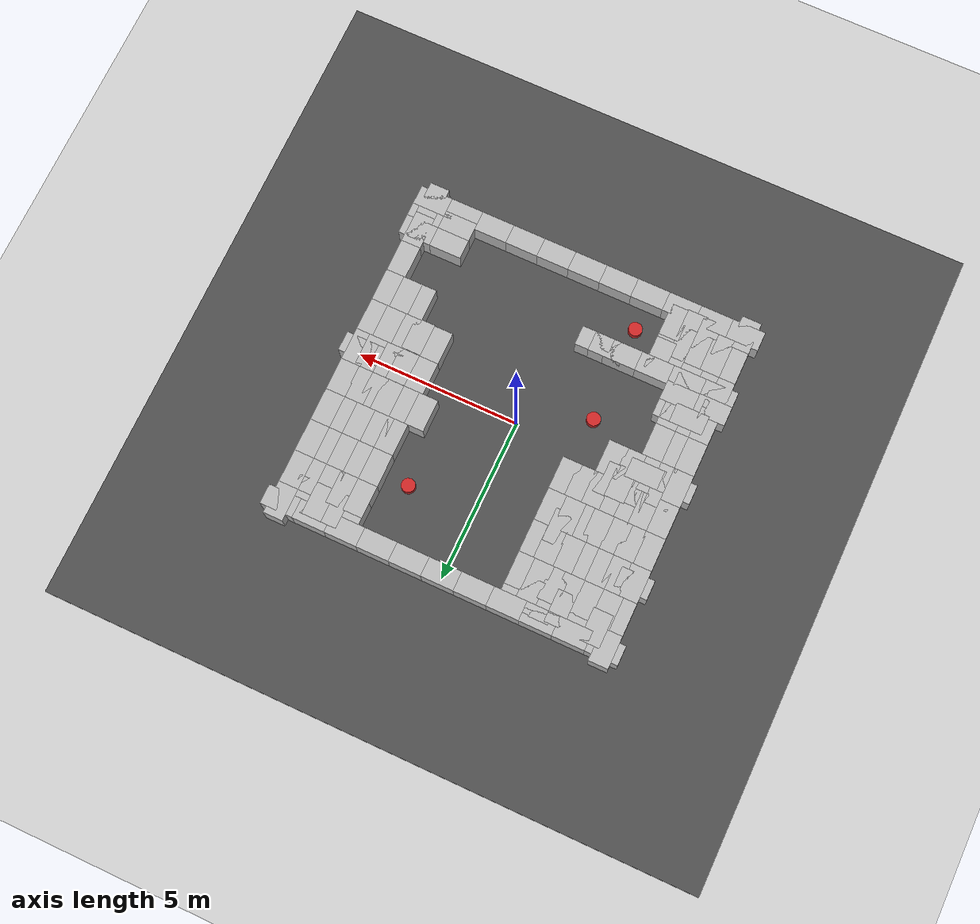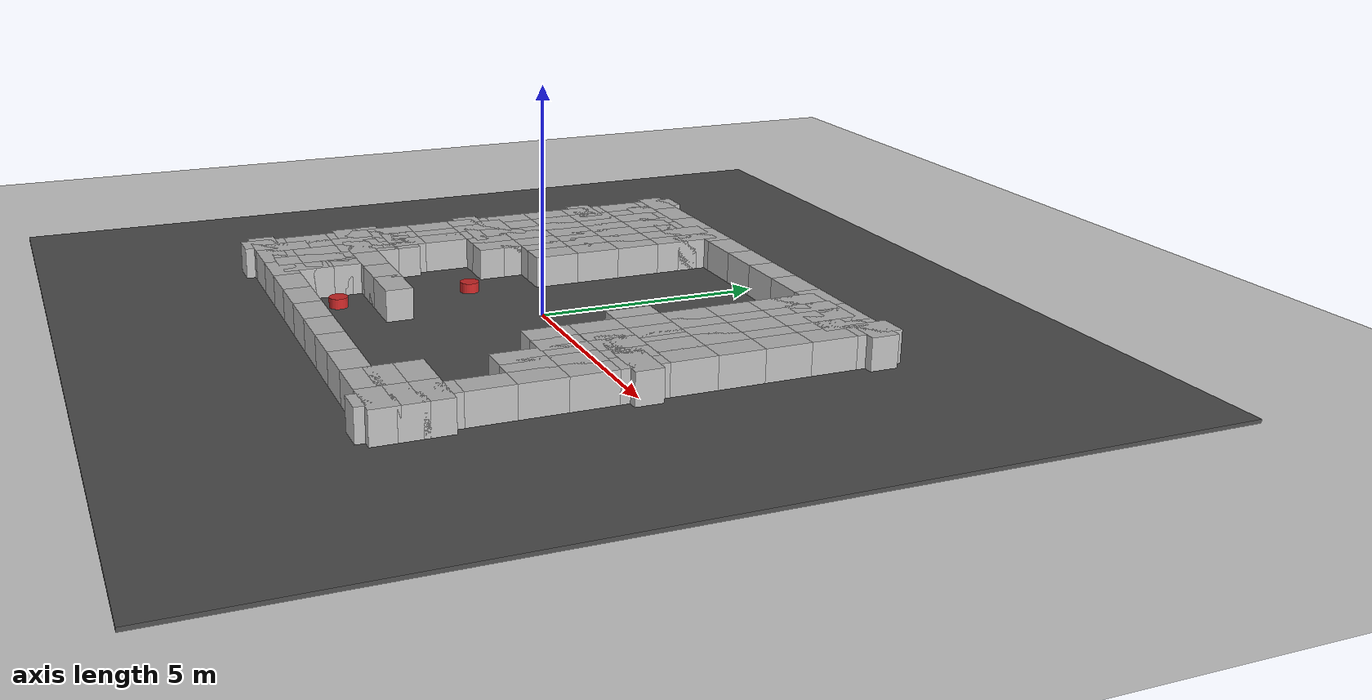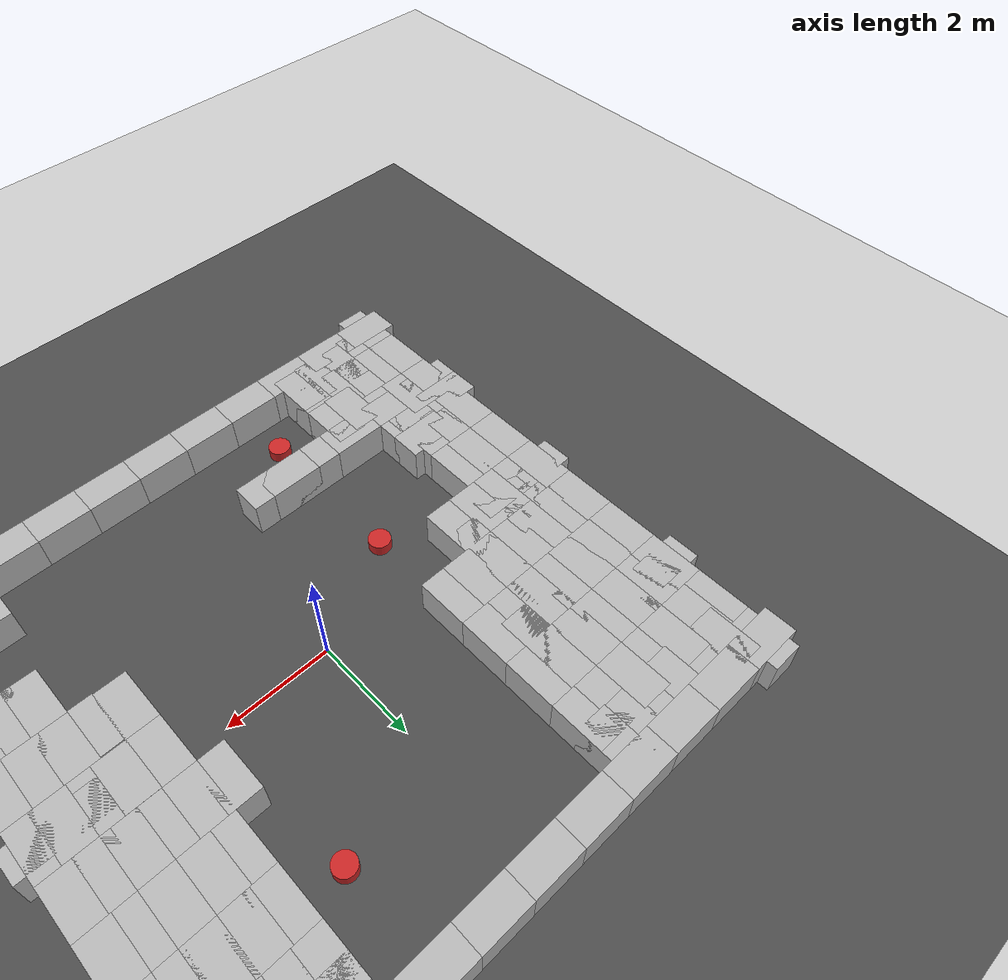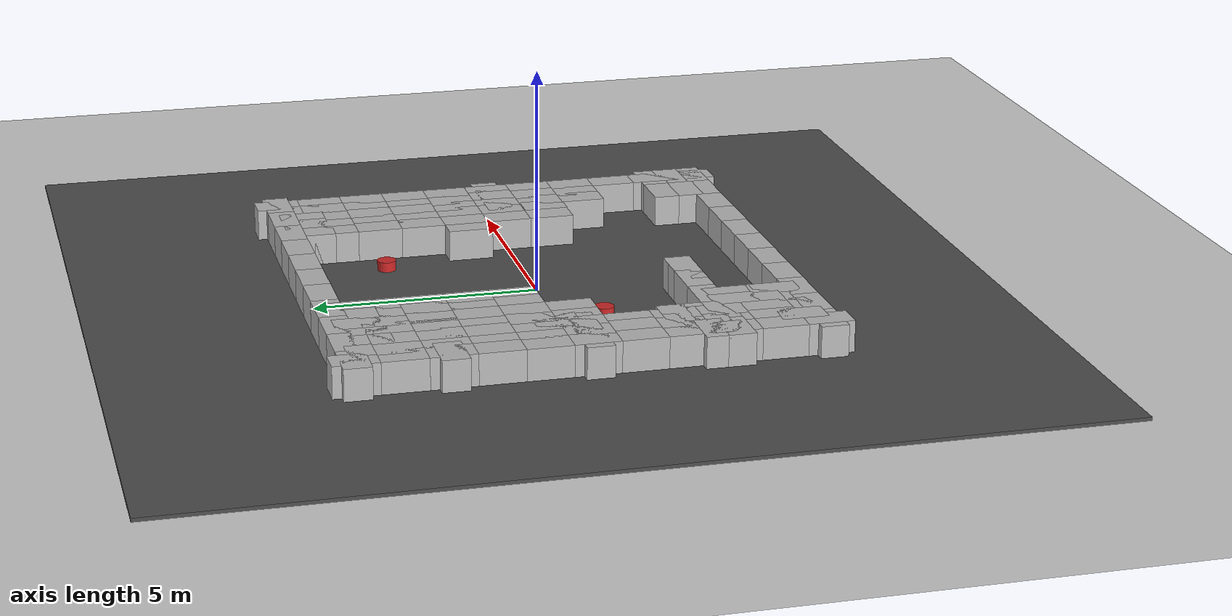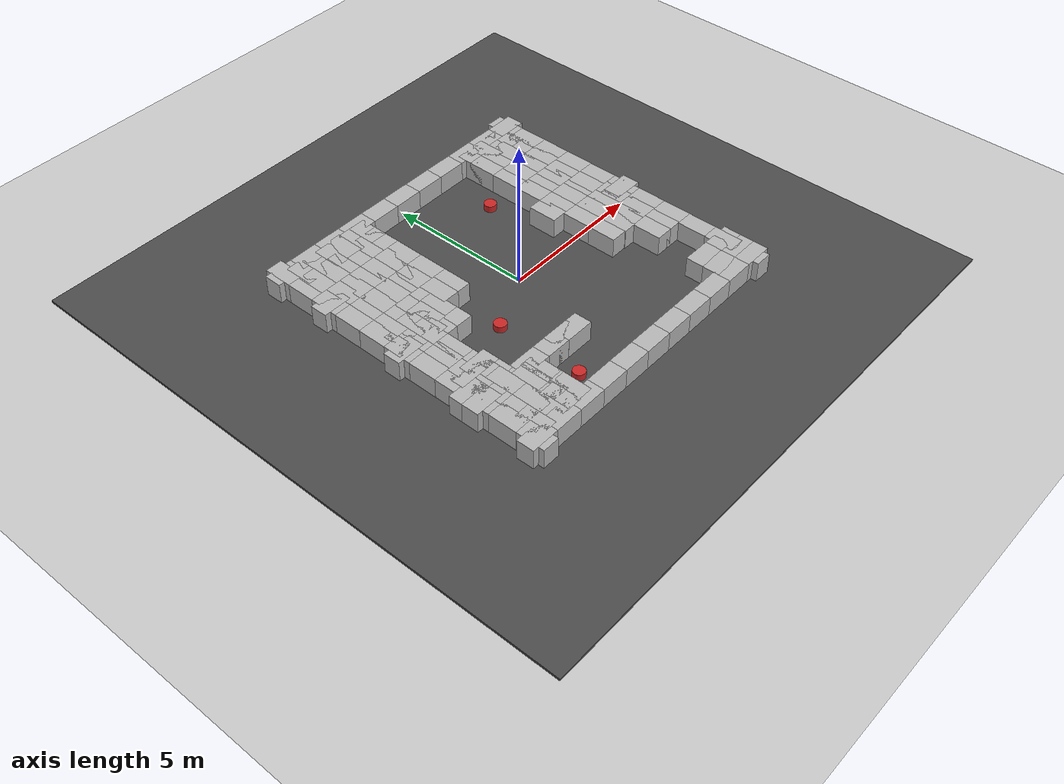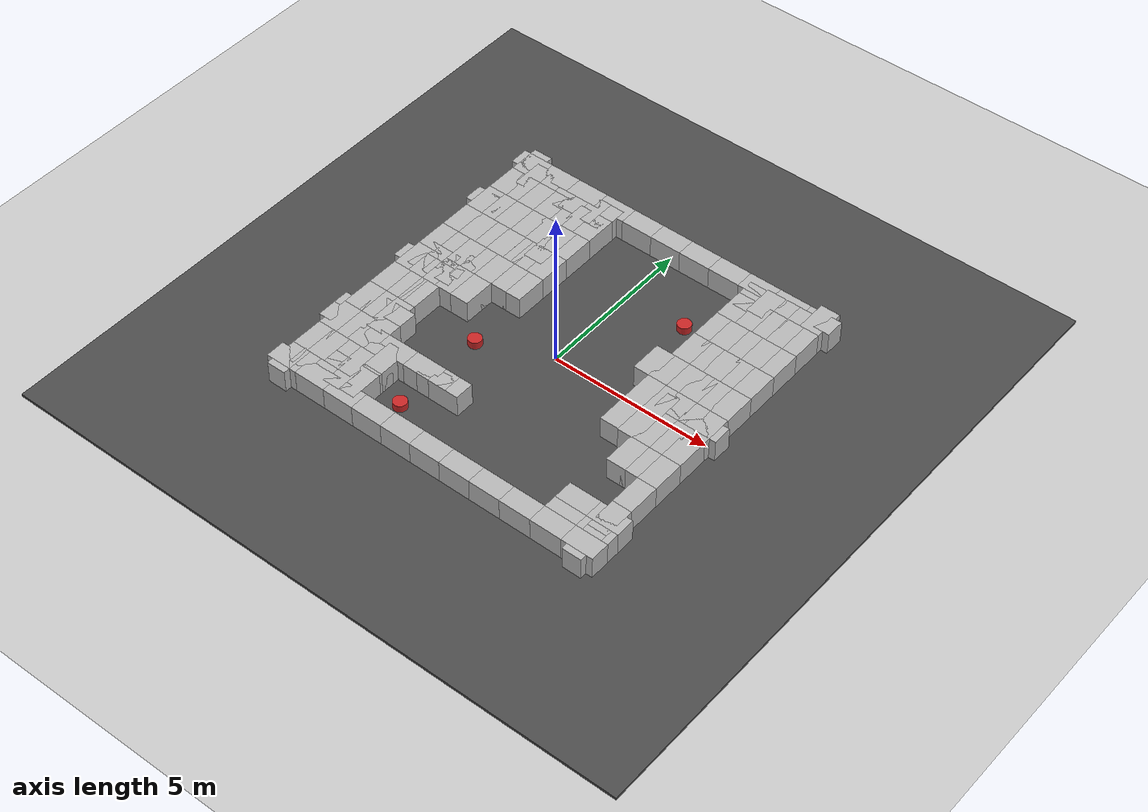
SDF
<sdf version="1.4">
 <world name="default">
  <light name="sun" type="directional">
   <pose>0 0 10 0 -0 0</pose>
   <diffuse>0.8 0.8 0.8 1</diffuse>
   <specular>0.2 0.2 0.2 1</specular>
   <attenuation>
    <range>1000</range>
    <constant>0.9</constant>
    <linear>0.01</linear>
    <quadratic>0.001</quadratic>
   </attenuation>
   <direction>-0.5 0.1 -0.9</direction>
  </light>
  <model name="ground_plane">
   <static>1</static>
   <link name="link">
    <collision name="collision">
     <geometry><plane><normal>0 0 1</normal><size>100 100</size></plane></geometry>
     <surface><friction><ode><mu>100</mu><mu2>50</mu2></ode></friction></surface>
    </collision>
    <visual name="visual">
     <cast_shadows>0</cast_shadows>
     <geometry><plane><normal>0 0 1</normal><size>100 100</size></plane></geometry>
     <material>
      <script><uri>file://media/materials/scripts/gazebo.material</uri><name>Gazebo/Grey</name></script>
     </material>
    </visual>
    <velocity_decay><linear>0</linear><angular>0</angular></velocity_decay>
   </link>
  </model>
  <physics type="ode">
   <max_step_size>0.001</max_step_size>
   <real_time_factor>1</real_time_factor>
   <real_time_update_rate>1000</real_time_update_rate>
   <gravity>0 0 -9.8</gravity>
  </physics>
  <scene><ambient>0.4 0.4 0.4 1</ambient><background>0.7 0.7 0.7 1</background><shadows>1</shadows></scene>
  <spherical_coordinates>
   <surface_model>EARTH_WGS84</surface_model>
   <latitude_deg>0</latitude_deg>
   <longitude_deg>0</longitude_deg>
   <elevation>0</elevation>
   <heading_deg>0</heading_deg>
  </spherical_coordinates>
  <model name="wall_0">
   <static>1</static>
   <link name="link">
    <pose>0 0 0.25 0 -0 0</pose>
    <collision name="collision"><geometry><box><size>1 0.6 1</size></box></geometry></collision>
    <visual name="visual">
     <geometry>
      <mesh><uri>model://brick_box_3x1x3/meshes/simple_box.dae</uri><scale>1 0.6 1</scale></mesh>
     </geometry>
     <material>
      <script>
       <uri>model://brick_box_3x1x3/materials/scripts</uri>
       <uri>model://brick_box_3x1x3/materials/textures</uri>
       <name>BrickBox/Diffuse</name>
      </script>
     </material>
    </visual>
    <velocity_decay><linear>0</linear><angular>0</angular></velocity_decay>
   </link>
   <pose>4 -5 0 0 -0 0</pose>
  </model>
  <model name="wall_1">
   <static>1</static>
   <link name="link">
    <pose>0 0 0.25 0 -0 0</pose>
    <collision name="collision"><geometry><box><size>1 0.6 1</size></box></geometry></collision>
    <visual name="visual">
     <geometry>
      <mesh><uri>model://brick_box_3x1x3/meshes/simple_box.dae</uri><scale>1 0.6 1</scale></mesh>
     </geometry>
     <material>
      <script>
       <uri>model://brick_box_3x1x3/materials/scripts</uri>
       <uri>model://brick_box_3x1x3/materials/textures</uri>
       <name>BrickBox/Diffuse</name>
      </script>
     </material>
    </visual>
    <velocity_decay><linear>0</linear><angular>0</angular></velocity_decay>
   </link>
   <pose>3 -5 0 0 -0 0</pose>
  </model>
  <model name="wall_2">
   <static>1</static>
   <link name="link">
    <pose>0 0 0.25 0 -0 0</pose>
    <collision name="collision"><geometry><box><size>1 0.6 1</size></box></geometry></collision>
    <visual name="visual">
     <geometry>
      <mesh><uri>model://brick_box_3x1x3/meshes/simple_box.dae</uri><scale>1 0.6 1</scale></mesh>
     </geometry>
     <material>
      <script>
       <uri>model://brick_box_3x1x3/materials/scripts</uri>
       <uri>model://brick_box_3x1x3/materials/textures</uri>
       <name>BrickBox/Diffuse</name>
      </script>
     </material>
    </visual>
    <velocity_decay><linear>0</linear><angular>0</angular></velocity_decay>
   </link>
   <pose>2 -5 0 0 -0 0</pose>
  </model>
  <model name="wall_3">
   <static>1</static>
   <link name="link">
    <pose>0 0 0.25 0 -0 0</pose>
    <collision name="collision"><geometry><box><size>1 0.6 1</size></box></geometry></collision>
    <visual name="visual">
     <geometry>
      <mesh><uri>model://brick_box_3x1x3/meshes/simple_box.dae</uri><scale>1 0.6 1</scale></mesh>
     </geometry>
     <material>
      <script>
       <uri>model://brick_box_3x1x3/materials/scripts</uri>
       <uri>model://brick_box_3x1x3/materials/textures</uri>
       <name>BrickBox/Diffuse</name>
      </script>
     </material>
    </visual>
    <velocity_decay><linear>0</linear><angular>0</angular></velocity_decay>
   </link>
   <pose>5 -5 0 0 -0 0</pose>
  </model>
  <model name="wall_4">
   <static>1</static>
   <link name="link">
    <pose>0 0 0.25 0 -0 0</pose>
    <collision name="collision"><geometry><box><size>0.6 1 1</size></box></geometry></collision>
    <visual name="visual">
     <geometry>
      <mesh><uri>model://brick_box_3x1x3/meshes/simple_box.dae</uri><scale>0.6 1 1</scale></mesh>
     </geometry>
     <material>
      <script>
       <uri>model://brick_box_3x1x3/materials/scripts</uri>
       <uri>model://brick_box_3x1x3/materials/textures</uri>
       <name>BrickBox/Diffuse</name>
      </script>
     </material>
    </visual>
    <velocity_decay><linear>0</linear><angular>0</angular></velocity_decay>
   </link>
   <pose>5 -5 0 0 -0 0</pose>
  </model>
  <model name="wall_5">
   <static>1</static>
   <link name="link">
    <pose>0 0 0.25 0 -0 0</pose>
    <collision name="collision"><geometry><box><size>0.6 1 1</size></box></geometry></collision>
    <visual name="visual">
     <geometry>
      <mesh><uri>model://brick_box_3x1x3/meshes/simple_box.dae</uri><scale>0.6 1 1</scale></mesh>
     </geometry>
     <material>
      <script>
       <uri>model://brick_box_3x1x3/materials/scripts</uri>
       <uri>model://brick_box_3x1x3/materials/textures</uri>
       <name>BrickBox/Diffuse</name>
      </script>
     </material>
    </visual>
    <velocity_decay><linear>0</linear><angular>0</angular></velocity_decay>
   </link>
   <pose>5 -4 0 0 -0 0</pose>
  </model>
  <model name="wall_6">
   <static>1</static>
   <link name="link">
    <pose>0 0 0.25 0 -0 0</pose>
    <collision name="collision"><geometry><box><size>1 0.6 1</size></box></geometry></collision>
    <visual name="visual">
     <geometry>
      <mesh><uri>model://brick_box_3x1x3/meshes/simple_box.dae</uri><scale>1 0.6 1</scale></mesh>
     </geometry>
     <material>
      <script>
       <uri>model://brick_box_3x1x3/materials/scripts</uri>
       <uri>model://brick_box_3x1x3/materials/textures</uri>
       <name>BrickBox/Diffuse</name>
      </script>
     </material>
    </visual>
    <velocity_decay><linear>0</linear><angular>0</angular></velocity_decay>
   </link>
   <pose>1 -5 0 0 -0 0</pose>
  </model>
  <model name="wall_7">
   <static>1</static>
   <link name="link">
    <pose>0 0 0.25 0 -0 0</pose>
    <collision name="collision"><geometry><box><size>1 0.6 1</size></box></geometry></collision>
    <visual name="visual">
     <geometry>
      <mesh><uri>model://brick_box_3x1x3/meshes/simple_box.dae</uri><scale>1 0.6 1</scale></mesh>
     </geometry>
     <material>
      <script>
       <uri>model://brick_box_3x1x3/materials/scripts</uri>
       <uri>model://brick_box_3x1x3/materials/textures</uri>
       <name>BrickBox/Diffuse</name>
      </script>
     </material>
    </visual>
    <velocity_decay><linear>0</linear><angular>0</angular></velocity_decay>
   </link>
   <pose>0 -5 0 0 -0 0</pose>
  </model>
  <model name="wall_8">
   <static>1</static>
   <link name="link">
    <pose>0 0 0.25 0 -0 0</pose>
    <collision name="collision"><geometry><box><size>1 0.6 1</size></box></geometry></collision>
    <visual name="visual">
     <geometry>
      <mesh><uri>model://brick_box_3x1x3/meshes/simple_box.dae</uri><scale>1 0.6 1</scale></mesh>
     </geometry>
     <material>
      <script>
       <uri>model://brick_box_3x1x3/materials/scripts</uri>
       <uri>model://brick_box_3x1x3/materials/textures</uri>
       <name>BrickBox/Diffuse</name>
      </script>
     </material>
    </visual>
    <velocity_decay><linear>0</linear><angular>0</angular></velocity_decay>
   </link>
   <pose>-1 -5 0 0 -0 0</pose>
  </model>
  <model name="wall_9">
   <static>1</static>
   <link name="link">
    <pose>0 0 0.25 0 -0 0</pose>
    <collision name="collision"><geometry><box><size>1 0.6 1</size></box></geometry></collision>
    <visual name="visual">
     <geometry>
      <mesh><uri>model://brick_box_3x1x3/meshes/simple_box.dae</uri><scale>1 0.6 1</scale></mesh>
     </geometry>
     <material>
      <script>
       <uri>model://brick_box_3x1x3/materials/scripts</uri>
       <uri>model://brick_box_3x1x3/materials/textures</uri>
       <name>BrickBox/Diffuse</name>
      </script>
     </material>
    </visual>
    <velocity_decay><linear>0</linear><angular>0</angular></velocity_decay>
   </link>
   <pose>-2 -5 0 0 -0 0</pose>
  </model>
  <model name="wall_10">
   <static>1</static>
   <link name="link">
    <pose>0 0 0.25 0 -0 0</pose>
    <collision name="collision"><geometry><box><size>1 0.6 1</size></box></geometry></collision>
    <visual name="visual">
     <geometry>
      <mesh><uri>model://brick_box_3x1x3/meshes/simple_box.dae</uri><scale>1 0.6 1</scale></mesh>
     </geometry>
     <material>
      <script>
       <uri>model://brick_box_3x1x3/materials/scripts</uri>
       <uri>model://brick_box_3x1x3/materials/textures</uri>
       <name>BrickBox/Diffuse</name>
      </script>
     </material>
    </visual>
    <velocity_decay><linear>0</linear><angular>0</angular></velocity_decay>
   </link>
   <pose>-3 -5 0 0 -0 0</pose>
  </model>
  <model name="wall_11">
   <static>1</static>
   <link name="link">
    <pose>0 0 0.25 0 -0 0</pose>
    <collision name="collision"><geometry><box><size>1 0.6 1</size></box></geometry></collision>
    <visual name="visual">
     <geometry>
      <mesh><uri>model://brick_box_3x1x3/meshes/simple_box.dae</uri><scale>1 0.6 1</scale></mesh>
     </geometry>
     <material>
      <script>
       <uri>model://brick_box_3x1x3/materials/scripts</uri>
       <uri>model://brick_box_3x1x3/materials/textures</uri>
       <name>BrickBox/Diffuse</name>
      </script>
     </material>
    </visual>
    <velocity_decay><linear>0</linear><angular>0</angular></velocity_decay>
   </link>
   <pose>-4 -5 0 0 -0 0</pose>
  </model>
  <model name="wall_12">
   <static>1</static>
   <link name="link">
    <pose>0 0 0.25 0 -0 0</pose>
    <collision name="collision"><geometry><box><size>1 0.6 1</size></box></geometry></collision>
    <visual name="visual">
     <geometry>
      <mesh><uri>model://brick_box_3x1x3/meshes/simple_box.dae</uri><scale>1 0.6 1</scale></mesh>
     </geometry>
     <material>
      <script>
       <uri>model://brick_box_3x1x3/materials/scripts</uri>
       <uri>model://brick_box_3x1x3/materials/textures</uri>
       <name>BrickBox/Diffuse</name>
      </script>
     </material>
    </visual>
    <velocity_decay><linear>0</linear><angular>0</angular></velocity_decay>
   </link>
   <pose>-5 -5 0 0 -0 0</pose>
  </model>
  <model name="wall_13">
   <static>1</static>
   <link name="link">
    <pose>0 0 0.25 0 -0 0</pose>
    <collision name="collision"><geometry><box><size>0.6 1 1</size></box></geometry></collision>
    <visual name="visual">
     <geometry>
      <mesh><uri>model://brick_box_3x1x3/meshes/simple_box.dae</uri><scale>0.6 1 1</scale></mesh>
     </geometry>
     <material>
      <script>
       <uri>model://brick_box_3x1x3/materials/scripts</uri>
       <uri>model://brick_box_3x1x3/materials/textures</uri>
       <name>BrickBox/Diffuse</name>
      </script>
     </material>
    </visual>
    <velocity_decay><linear>0</linear><angular>0</angular></velocity_decay>
   </link>
   <pose>5 -3 0 0 -0 0</pose>
  </model>
  <model name="wall_14">
   <static>1</static>
   <link name="link">
    <pose>0 0 0.25 0 -0 0</pose>
    <collision name="collision"><geometry><box><size>0.6 1 1</size></box></geometry></collision>
    <visual name="visual">
     <geometry>
      <mesh><uri>model://brick_box_3x1x3/meshes/simple_box.dae</uri><scale>0.6 1 1</scale></mesh>
     </geometry>
     <material>
      <script>
       <uri>model://brick_box_3x1x3/materials/scripts</uri>
       <uri>model://brick_box_3x1x3/materials/textures</uri>
       <name>BrickBox/Diffuse</name>
      </script>
     </material>
    </visual>
    <velocity_decay><linear>0</linear><angular>0</angular></velocity_decay>
   </link>
   <pose>5 -2 0 0 -0 0</pose>
  </model>
  <model name="wall_15">
   <static>1</static>
   <link name="link">
    <pose>0 0 0.25 0 -0 0</pose>
    <collision name="collision"><geometry><box><size>0.6 1 1</size></box></geometry></collision>
    <visual name="visual">
     <geometry>
      <mesh><uri>model://brick_box_3x1x3/meshes/simple_box.dae</uri><scale>0.6 1 1</scale></mesh>
     </geometry>
     <material>
      <script>
       <uri>model://brick_box_3x1x3/materials/scripts</uri>
       <uri>model://brick_box_3x1x3/materials/textures</uri>
       <name>BrickBox/Diffuse</name>
      </script>
     </material>
    </visual>
    <velocity_decay><linear>0</linear><angular>0</angular></velocity_decay>
   </link>
   <pose>5 -1 0 0 -0 0</pose>
  </model>
  <model name="wall_16">
   <static>1</static>
   <link name="link">
    <pose>0 0 0.25 0 -0 0</pose>
    <collision name="collision"><geometry><box><size>0.6 1 1</size></box></geometry></collision>
    <visual name="visual">
     <geometry>
      <mesh><uri>model://brick_box_3x1x3/meshes/simple_box.dae</uri><scale>0.6 1 1</scale></mesh>
     </geometry>
     <material>
      <script>
       <uri>model://brick_box_3x1x3/materials/scripts</uri>
       <uri>model://brick_box_3x1x3/materials/textures</uri>
       <name>BrickBox/Diffuse</name>
      </script>
     </material>
    </visual>
    <velocity_decay><linear>0</linear><angular>0</angular></velocity_decay>
   </link>
   <pose>5 0 0 0 -0 0</pose>
  </model>
  <model name="wall_17">
   <static>1</static>
   <link name="link">
    <pose>0 0 0.25 0 -0 0</pose>
    <collision name="collision"><geometry><box><size>0.6 1 1</size></box></geometry></collision>
    <visual name="visual">
     <geometry>
      <mesh><uri>model://brick_box_3x1x3/meshes/simple_box.dae</uri><scale>0.6 1 1</scale></mesh>
     </geometry>
     <material>
      <script>
       <uri>model://brick_box_3x1x3/materials/scripts</uri>
       <uri>model://brick_box_3x1x3/materials/textures</uri>
       <name>BrickBox/Diffuse</name>
      </script>
     </material>
    </visual>
    <velocity_decay><linear>0</linear><angular>0</angular></velocity_decay>
   </link>
   <pose>5 1 0 0 -0 0</pose>
  </model>
  <model name="wall_18">
   <static>1</static>
   <link name="link">
    <pose>0 0 0.25 0 -0 0</pose>
    <collision name="collision"><geometry><box><size>0.6 1 1</size></box></geometry></collision>
    <visual name="visual">
     <geometry>
      <mesh><uri>model://brick_box_3x1x3/meshes/simple_box.dae</uri><scale>0.6 1 1</scale></mesh>
     </geometry>
     <material>
      <script>
       <uri>model://brick_box_3x1x3/materials/scripts</uri>
       <uri>model://brick_box_3x1x3/materials/textures</uri>
       <name>BrickBox/Diffuse</name>
      </script>
     </material>
    </visual>
    <velocity_decay><linear>0</linear><angular>0</angular></velocity_decay>
   </link>
   <pose>5 2 0 0 -0 0</pose>
  </model>
  <model name="wall_19">
   <static>1</static>
   <link name="link">
    <pose>0 0 0.25 0 -0 0</pose>
    <collision name="collision"><geometry><box><size>0.6 1 1</size></box></geometry></collision>
    <visual name="visual">
     <geometry>
      <mesh><uri>model://brick_box_3x1x3/meshes/simple_box.dae</uri><scale>0.6 1 1</scale></mesh>
     </geometry>
     <material>
      <script>
       <uri>model://brick_box_3x1x3/materials/scripts</uri>
       <uri>model://brick_box_3x1x3/materials/textures</uri>
       <name>BrickBox/Diffuse</name>
      </script>
     </material>
    </visual>
    <velocity_decay><linear>0</linear><angular>0</angular></velocity_decay>
   </link>
   <pose>5 3 0 0 -0 0</pose>
  </model>
  <model name="wall_20">
   <static>1</static>
   <link name="link">
    <pose>0 0 0.25 0 -0 0</pose>
    <collision name="collision"><geometry><box><size>0.6 1 1</size></box></geometry></collision>
    <visual name="visual">
     <geometry>
      <mesh><uri>model://brick_box_3x1x3/meshes/simple_box.dae</uri><scale>0.6 1 1</scale></mesh>
     </geometry>
     <material>
      <script>
       <uri>model://brick_box_3x1x3/materials/scripts</uri>
       <uri>model://brick_box_3x1x3/materials/textures</uri>
       <name>BrickBox/Diffuse</name>
      </script>
     </material>
    </visual>
    <velocity_decay><linear>0</linear><angular>0</angular></velocity_decay>
   </link>
   <pose>5 4 0 0 -0 0</pose>
  </model>
  <model name="wall_21">
   <static>1</static>
   <link name="link">
    <pose>0 0 0.25 0 -0 0</pose>
    <collision name="collision"><geometry><box><size>0.6 1 1</size></box></geometry></collision>
    <visual name="visual">
     <geometry>
      <mesh><uri>model://brick_box_3x1x3/meshes/simple_box.dae</uri><scale>0.6 1 1</scale></mesh>
     </geometry>
     <material>
      <script>
       <uri>model://brick_box_3x1x3/materials/scripts</uri>
       <uri>model://brick_box_3x1x3/materials/textures</uri>
       <name>BrickBox/Diffuse</name>
      </script>
     </material>
    </visual>
    <velocity_decay><linear>0</linear><angular>0</angular></velocity_decay>
   </link>
   <pose>5 5 0 0 -0 0</pose>
  </model>
  <model name="wall_22">
   <static>1</static>
   <link name="link">
    <pose>0 0 0.25 0 -0 0</pose>
    <collision name="collision"><geometry><box><size>1 0.6 1</size></box></geometry></collision>
    <visual name="visual">
     <geometry>
      <mesh><uri>model://brick_box_3x1x3/meshes/simple_box.dae</uri><scale>1 0.6 1</scale></mesh>
     </geometry>
     <material>
      <script>
       <uri>model://brick_box_3x1x3/materials/scripts</uri>
       <uri>model://brick_box_3x1x3/materials/textures</uri>
       <name>BrickBox/Diffuse</name>
      </script>
     </material>
    </visual>
    <velocity_decay><linear>0</linear><angular>0</angular></velocity_decay>
   </link>
   <pose>4 5 0 0 -0 0</pose>
  </model>
  <model name="wall_23">
   <static>1</static>
   <link name="link">
    <pose>0 0 0.25 0 -0 0</pose>
    <collision name="collision"><geometry><box><size>1 0.6 1</size></box></geometry></collision>
    <visual name="visual">
     <geometry>
      <mesh><uri>model://brick_box_3x1x3/meshes/simple_box.dae</uri><scale>1 0.6 1</scale></mesh>
     </geometry>
     <material>
      <script>
       <uri>model://brick_box_3x1x3/materials/scripts</uri>
       <uri>model://brick_box_3x1x3/materials/textures</uri>
       <name>BrickBox/Diffuse</name>
      </script>
     </material>
    </visual>
    <velocity_decay><linear>0</linear><angular>0</angular></velocity_decay>
   </link>
   <pose>5 5 0 0 -0 0</pose>
  </model>
  <model name="wall_24">
   <static>1</static>
   <link name="link">
    <pose>0 0 0.25 0 -0 0</pose>
    <collision name="collision"><geometry><box><size>1 0.6 1</size></box></geometry></collision>
    <visual name="visual">
     <geometry>
      <mesh><uri>model://brick_box_3x1x3/meshes/simple_box.dae</uri><scale>1 0.6 1</scale></mesh>
     </geometry>
     <material>
      <script>
       <uri>model://brick_box_3x1x3/materials/scripts</uri>
       <uri>model://brick_box_3x1x3/materials/textures</uri>
       <name>BrickBox/Diffuse</name>
      </script>
     </material>
    </visual>
    <velocity_decay><linear>0</linear><angular>0</angular></velocity_decay>
   </link>
   <pose>3 5 0 0 -0 0</pose>
  </model>
  <model name="wall_25">
   <static>1</static>
   <link name="link">
    <pose>0 0 0.25 0 -0 0</pose>
    <collision name="collision"><geometry><box><size>1 0.6 1</size></box></geometry></collision>
    <visual name="visual">
     <geometry>
      <mesh><uri>model://brick_box_3x1x3/meshes/simple_box.dae</uri><scale>1 0.6 1</scale></mesh>
     </geometry>
     <material>
      <script>
       <uri>model://brick_box_3x1x3/materials/scripts</uri>
       <uri>model://brick_box_3x1x3/materials/textures</uri>
       <name>BrickBox/Diffuse</name>
      </script>
     </material>
    </visual>
    <velocity_decay><linear>0</linear><angular>0</angular></velocity_decay>
   </link>
   <pose>2 5 0 0 -0 0</pose>
  </model>
  <model name="wall_26">
   <static>1</static>
   <link name="link">
    <pose>0 0 0.25 0 -0 0</pose>
    <collision name="collision"><geometry><box><size>1 0.6 1</size></box></geometry></collision>
    <visual name="visual">
     <geometry>
      <mesh><uri>model://brick_box_3x1x3/meshes/simple_box.dae</uri><scale>1 0.6 1</scale></mesh>
     </geometry>
     <material>
      <script>
       <uri>model://brick_box_3x1x3/materials/scripts</uri>
       <uri>model://brick_box_3x1x3/materials/textures</uri>
       <name>BrickBox/Diffuse</name>
      </script>
     </material>
    </visual>
    <velocity_decay><linear>0</linear><angular>0</angular></velocity_decay>
   </link>
   <pose>1 5 0 0 -0 0</pose>
  </model>
  <model name="wall_28">
   <static>1</static>
   <link name="link">
    <pose>0 0 0.25 0 -0 0</pose>
    <collision name="collision"><geometry><box><size>1 0.6 1</size></box></geometry></collision>
    <visual name="visual">
     <geometry>
      <mesh><uri>model://brick_box_3x1x3/meshes/simple_box.dae</uri><scale>1 0.6 1</scale></mesh>
     </geometry>
     <material>
      <script>
       <uri>model://brick_box_3x1x3/materials/scripts</uri>
       <uri>model://brick_box_3x1x3/materials/textures</uri>
       <name>BrickBox/Diffuse</name>
      </script>
     </material>
    </visual>
    <velocity_decay><linear>0</linear><angular>0</angular></velocity_decay>
   </link>
   <pose>-1 5 0 0 -0 0</pose>
  </model>
  <model name="wall_29">
   <static>1</static>
   <link name="link">
    <pose>0 0 0.25 0 -0 0</pose>
    <collision name="collision"><geometry><box><size>1 0.6 1</size></box></geometry></collision>
    <visual name="visual">
     <geometry>
      <mesh><uri>model://brick_box_3x1x3/meshes/simple_box.dae</uri><scale>1 0.6 1</scale></mesh>
     </geometry>
     <material>
      <script>
       <uri>model://brick_box_3x1x3/materials/scripts</uri>
       <uri>model://brick_box_3x1x3/materials/textures</uri>
       <name>BrickBox/Diffuse</name>
      </script>
     </material>
    </visual>
    <velocity_decay><linear>0</linear><angular>0</angular></velocity_decay>
   </link>
   <pose>-2 5 0 0 -0 0</pose>
  </model>
  <model name="wall_30">
   <static>1</static>
   <link name="link">
    <pose>0 0 0.25 0 -0 0</pose>
    <collision name="collision"><geometry><box><size>1 0.6 1</size></box></geometry></collision>
    <visual name="visual">
     <geometry>
      <mesh><uri>model://brick_box_3x1x3/meshes/simple_box.dae</uri><scale>1 0.6 1</scale></mesh>
     </geometry>
     <material>
      <script>
       <uri>model://brick_box_3x1x3/materials/scripts</uri>
       <uri>model://brick_box_3x1x3/materials/textures</uri>
       <name>BrickBox/Diffuse</name>
      </script>
     </material>
    </visual>
    <velocity_decay><linear>0</linear><angular>0</angular></velocity_decay>
   </link>
   <pose>-3 5 0 0 -0 0</pose>
  </model>
  <model name="wall_31">
   <static>1</static>
   <link name="link">
    <pose>0 0 0.25 0 -0 0</pose>
    <collision name="collision"><geometry><box><size>1 0.6 1</size></box></geometry></collision>
    <visual name="visual">
     <geometry>
      <mesh><uri>model://brick_box_3x1x3/meshes/simple_box.dae</uri><scale>1 0.6 1</scale></mesh>
     </geometry>
     <material>
      <script>
       <uri>model://brick_box_3x1x3/materials/scripts</uri>
       <uri>model://brick_box_3x1x3/materials/textures</uri>
       <name>BrickBox/Diffuse</name>
      </script>
     </material>
    </visual>
    <velocity_decay><linear>0</linear><angular>0</angular></velocity_decay>
   </link>
   <pose>-4 5 0 0 -0 0</pose>
  </model>
  <model name="wall_32">
   <static>1</static>
   <link name="link">
    <pose>0 0 0.25 0 -0 0</pose>
    <collision name="collision"><geometry><box><size>1 0.6 1</size></box></geometry></collision>
    <visual name="visual">
     <geometry>
      <mesh><uri>model://brick_box_3x1x3/meshes/simple_box.dae</uri><scale>1 0.6 1</scale></mesh>
     </geometry>
     <material>
      <script>
       <uri>model://brick_box_3x1x3/materials/scripts</uri>
       <uri>model://brick_box_3x1x3/materials/textures</uri>
       <name>BrickBox/Diffuse</name>
      </script>
     </material>
    </visual>
    <velocity_decay><linear>0</linear><angular>0</angular></velocity_decay>
   </link>
   <pose>-5 5 0 0 -0 0</pose>
  </model>
  <model name="wall_33">
   <static>1</static>
   <link name="link">
    <pose>0 0 0.25 0 -0 0</pose>
    <collision name="collision"><geometry><box><size>0.6 1 1</size></box></geometry></collision>
    <visual name="visual">
     <geometry>
      <mesh><uri>model://brick_box_3x1x3/meshes/simple_box.dae</uri><scale>0.6 1 1</scale></mesh>
     </geometry>
     <material>
      <script>
       <uri>model://brick_box_3x1x3/materials/scripts</uri>
       <uri>model://brick_box_3x1x3/materials/textures</uri>
       <name>BrickBox/Diffuse</name>
      </script>
     </material>
    </visual>
    <velocity_decay><linear>0</linear><angular>0</angular></velocity_decay>
   </link>
   <pose>-5 -5 0 0 -0 0</pose>
  </model>
  <model name="wall_34">
   <static>1</static>
   <link name="link">
    <pose>0 0 0.25 0 -0 0</pose>
    <collision name="collision"><geometry><box><size>0.6 1 1</size></box></geometry></collision>
    <visual name="visual">
     <geometry>
      <mesh><uri>model://brick_box_3x1x3/meshes/simple_box.dae</uri><scale>0.6 1 1</scale></mesh>
     </geometry>
     <material>
      <script>
       <uri>model://brick_box_3x1x3/materials/scripts</uri>
       <uri>model://brick_box_3x1x3/materials/textures</uri>
       <name>BrickBox/Diffuse</name>
      </script>
     </material>
    </visual>
    <velocity_decay><linear>0</linear><angular>0</angular></velocity_decay>
   </link>
   <pose>-5 -4 0 0 -0 0</pose>
  </model>
  <model name="wall_35">
   <static>1</static>
   <link name="link">
    <pose>0 0 0.25 0 -0 0</pose>
    <collision name="collision"><geometry><box><size>0.6 1 1</size></box></geometry></collision>
    <visual name="visual">
     <geometry>
      <mesh><uri>model://brick_box_3x1x3/meshes/simple_box.dae</uri><scale>0.6 1 1</scale></mesh>
     </geometry>
     <material>
      <script>
       <uri>model://brick_box_3x1x3/materials/scripts</uri>
       <uri>model://brick_box_3x1x3/materials/textures</uri>
       <name>BrickBox/Diffuse</name>
      </script>
     </material>
    </visual>
    <velocity_decay><linear>0</linear><angular>0</angular></velocity_decay>
   </link>
   <pose>-5 -3 0 0 -0 0</pose>
  </model>
  <model name="wall_36">
   <static>1</static>
   <link name="link">
    <pose>0 0 0.25 0 -0 0</pose>
    <collision name="collision"><geometry><box><size>0.6 1 1</size></box></geometry></collision>
    <visual name="visual">
     <geometry>
      <mesh><uri>model://brick_box_3x1x3/meshes/simple_box.dae</uri><scale>0.6 1 1</scale></mesh>
     </geometry>
     <material>
      <script>
       <uri>model://brick_box_3x1x3/materials/scripts</uri>
       <uri>model://brick_box_3x1x3/materials/textures</uri>
       <name>BrickBox/Diffuse</name>
      </script>
     </material>
    </visual>
    <velocity_decay><linear>0</linear><angular>0</angular></velocity_decay>
   </link>
   <pose>-5 -2 0 0 -0 0</pose>
  </model>
  <model name="wall_37">
   <static>1</static>
   <link name="link">
    <pose>0 0 0.25 0 -0 0</pose>
    <collision name="collision"><geometry><box><size>0.6 1 1</size></box></geometry></collision>
    <visual name="visual">
     <geometry>
      <mesh><uri>model://brick_box_3x1x3/meshes/simple_box.dae</uri><scale>0.6 1 1</scale></mesh>
     </geometry>
     <material>
      <script>
       <uri>model://brick_box_3x1x3/materials/scripts</uri>
       <uri>model://brick_box_3x1x3/materials/textures</uri>
       <name>BrickBox/Diffuse</name>
      </script>
     </material>
    </visual>
    <velocity_decay><linear>0</linear><angular>0</angular></velocity_decay>
   </link>
   <pose>-5 -1 0 0 -0 0</pose>
  </model>
  <model name="wall_38">
   <static>1</static>
   <link name="link">
    <pose>0 0 0.25 0 -0 0</pose>
    <collision name="collision"><geometry><box><size>0.6 1 1</size></box></geometry></collision>
    <visual name="visual">
     <geometry>
      <mesh><uri>model://brick_box_3x1x3/meshes/simple_box.dae</uri><scale>0.6 1 1</scale></mesh>
     </geometry>
     <material>
      <script>
       <uri>model://brick_box_3x1x3/materials/scripts</uri>
       <uri>model://brick_box_3x1x3/materials/textures</uri>
       <name>BrickBox/Diffuse</name>
      </script>
     </material>
    </visual>
    <velocity_decay><linear>0</linear><angular>0</angular></velocity_decay>
   </link>
   <pose>-5 0 0 0 -0 0</pose>
  </model>
  <model name="wall_39">
   <static>1</static>
   <link name="link">
    <pose>0 0 0.25 0 -0 0</pose>
    <collision name="collision"><geometry><box><size>0.6 1 1</size></box></geometry></collision>
    <visual name="visual">
     <geometry>
      <mesh><uri>model://brick_box_3x1x3/meshes/simple_box.dae</uri><scale>0.6 1 1</scale></mesh>
     </geometry>
     <material>
      <script>
       <uri>model://brick_box_3x1x3/materials/scripts</uri>
       <uri>model://brick_box_3x1x3/materials/textures</uri>
       <name>BrickBox/Diffuse</name>
      </script>
     </material>
    </visual>
    <velocity_decay><linear>0</linear><angular>0</angular></velocity_decay>
   </link>
   <pose>-5 1 0 0 -0 0</pose>
  </model>
  <model name="wall_40">
   <static>1</static>
   <link name="link">
    <pose>0 0 0.25 0 -0 0</pose>
    <collision name="collision"><geometry><box><size>0.6 1 1</size></box></geometry></collision>
    <visual name="visual">
     <geometry>
      <mesh><uri>model://brick_box_3x1x3/meshes/simple_box.dae</uri><scale>0.6 1 1</scale></mesh>
     </geometry>
     <material>
      <script>
       <uri>model://brick_box_3x1x3/materials/scripts</uri>
       <uri>model://brick_box_3x1x3/materials/textures</uri>
       <name>BrickBox/Diffuse</name>
      </script>
     </material>
    </visual>
    <velocity_decay><linear>0</linear><angular>0</angular></velocity_decay>
   </link>
   <pose>-5 2 0 0 -0 0</pose>
  </model>
  <model name="wall_41">
   <static>1</static>
   <link name="link">
    <pose>0 0 0.25 0 -0 0</pose>
    <collision name="collision"><geometry><box><size>0.6 1 1</size></box></geometry></collision>
    <visual name="visual">
     <geometry>
      <mesh><uri>model://brick_box_3x1x3/meshes/simple_box.dae</uri><scale>0.6 1 1</scale></mesh>
     </geometry>
     <material>
      <script>
       <uri>model://brick_box_3x1x3/materials/scripts</uri>
       <uri>model://brick_box_3x1x3/materials/textures</uri>
       <name>BrickBox/Diffuse</name>
      </script>
     </material>
    </visual>
    <velocity_decay><linear>0</linear><angular>0</angular></velocity_decay>
   </link>
   <pose>-5 3 0 0 -0 0</pose>
  </model>
  <model name="wall_42">
   <static>1</static>
   <link name="link">
    <pose>0 0 0.25 0 -0 0</pose>
    <collision name="collision"><geometry><box><size>0.6 1 1</size></box></geometry></collision>
    <visual name="visual">
     <geometry>
      <mesh><uri>model://brick_box_3x1x3/meshes/simple_box.dae</uri><scale>0.6 1 1</scale></mesh>
     </geometry>
     <material>
      <script>
       <uri>model://brick_box_3x1x3/materials/scripts</uri>
       <uri>model://brick_box_3x1x3/materials/textures</uri>
       <name>BrickBox/Diffuse</name>
      </script>
     </material>
    </visual>
    <velocity_decay><linear>0</linear><angular>0</angular></velocity_decay>
   </link>
   <pose>-5 4 0 0 -0 0</pose>
  </model>
  <model name="wall_43">
   <static>1</static>
   <link name="link">
    <pose>0 0 0.25 0 -0 0</pose>
    <collision name="collision"><geometry><box><size>0.6 1 1</size></box></geometry></collision>
    <visual name="visual">
     <geometry>
      <mesh><uri>model://brick_box_3x1x3/meshes/simple_box.dae</uri><scale>0.6 1 1</scale></mesh>
     </geometry>
     <material>
      <script>
       <uri>model://brick_box_3x1x3/materials/scripts</uri>
       <uri>model://brick_box_3x1x3/materials/textures</uri>
       <name>BrickBox/Diffuse</name>
      </script>
     </material>
    </visual>
    <velocity_decay><linear>0</linear><angular>0</angular></velocity_decay>
   </link>
   <pose>-5 5 0 0 -0 0</pose>
  </model>
  <model name="wall">
   <static>1</static>
   <link name="link">
    <pose>0 0 0.25 0 -0 0</pose>
    <collision name="collision"><geometry><box><size>1 0.6 1</size></box></geometry></collision>
    <visual name="visual">
     <geometry>
      <mesh><uri>model://brick_box_3x1x3/meshes/simple_box.dae</uri><scale>1 0.6 1</scale></mesh>
     </geometry>
     <material>
      <script>
       <uri>model://brick_box_3x1x3/materials/scripts</uri>
       <uri>model://brick_box_3x1x3/materials/textures</uri>
       <name>BrickBox/Diffuse</name>
      </script>
     </material>
    </visual>
    <velocity_decay><linear>0</linear><angular>0</angular></velocity_decay>
   </link>
   <pose>-5 0 0 0 -0 0</pose>
  </model>
  <model name="wall_44">
   <static>1</static>
   <link name="link">
    <pose>0 0 0.25 0 -0 0</pose>
    <collision name="collision"><geometry><box><size>1 0.6 1</size></box></geometry></collision>
    <visual name="visual">
     <geometry>
      <mesh><uri>model://brick_box_3x1x3/meshes/simple_box.dae</uri><scale>1 0.6 1</scale></mesh>
     </geometry>
     <material>
      <script>
       <uri>model://brick_box_3x1x3/materials/scripts</uri>
       <uri>model://brick_box_3x1x3/materials/textures</uri>
       <name>BrickBox/Diffuse</name>
      </script>
     </material>
    </visual>
    <velocity_decay><linear>0</linear><angular>0</angular></velocity_decay>
   </link>
   <pose>-4 0 0 0 -0 0</pose>
  </model>
  <model name="wall_46">
   <static>1</static>
   <link name="link">
    <pose>0 0 0.25 0 -0 0</pose>
    <collision name="collision"><geometry><box><size>1 0.6 1</size></box></geometry></collision>
    <visual name="visual">
     <geometry>
      <mesh><uri>model://brick_box_3x1x3/meshes/simple_box.dae</uri><scale>1 0.6 1</scale></mesh>
     </geometry>
     <material>
      <script>
       <uri>model://brick_box_3x1x3/materials/scripts</uri>
       <uri>model://brick_box_3x1x3/materials/textures</uri>
       <name>BrickBox/Diffuse</name>
      </script>
     </material>
    </visual>
    <velocity_decay><linear>0</linear><angular>0</angular></velocity_decay>
   </link>
   <pose>5 0 0 0 -0 0</pose>
  </model>
  <model name="wall_47">
   <static>1</static>
   <link name="link">
    <pose>0 0 0.25 0 -0 0</pose>
    <collision name="collision"><geometry><box><size>1 0.6 1</size></box></geometry></collision>
    <visual name="visual">
     <geometry>
      <mesh><uri>model://brick_box_3x1x3/meshes/simple_box.dae</uri><scale>1 0.6 1</scale></mesh>
     </geometry>
     <material>
      <script>
       <uri>model://brick_box_3x1x3/materials/scripts</uri>
       <uri>model://brick_box_3x1x3/materials/textures</uri>
       <name>BrickBox/Diffuse</name>
      </script>
     </material>
    </visual>
    <velocity_decay><linear>0</linear><angular>0</angular></velocity_decay>
   </link>
   <pose>4 0 0 0 -0 0</pose>
  </model>
  <model name="wall_66">
   <static>1</static>
   <link name="link">
    <pose>0 0 0.25 0 -0 0</pose>
    <collision name="collision"><geometry><box><size>1 0.6 1</size></box></geometry></collision>
    <visual name="visual">
     <geometry>
      <mesh><uri>model://brick_box_3x1x3/meshes/simple_box.dae</uri><scale>1 0.6 1</scale></mesh>
     </geometry>
     <material>
      <script>
       <uri>model://brick_box_3x1x3/materials/scripts</uri>
       <uri>model://brick_box_3x1x3/materials/textures</uri>
       <name>BrickBox/Diffuse</name>
      </script>
     </material>
    </visual>
    <velocity_decay><linear>0</linear><angular>0</angular></velocity_decay>
   </link>
   <pose>0 5 0 0 -0 0</pose>
  </model>
  <model name="wall_69">
   <static>1</static>
   <link name="link">
    <pose>0 0 0.25 0 -0 0</pose>
    <collision name="collision"><geometry><box><size>1 0.6 1</size></box></geometry></collision>
    <visual name="visual">
     <geometry>
      <mesh><uri>model://brick_box_3x1x3/meshes/simple_box.dae</uri><scale>1 0.6 1</scale></mesh>
     </geometry>
     <material>
      <script>
       <uri>model://brick_box_3x1x3/materials/scripts</uri>
       <uri>model://brick_box_3x1x3/materials/textures</uri>
       <name>BrickBox/Diffuse</name>
      </script>
     </material>
    </visual>
    <velocity_decay><linear>0</linear><angular>0</angular></velocity_decay>
   </link>
   <pose>-5 -3 0 0 -0 0</pose>
  </model>
  <model name="wall_70">
   <static>1</static>
   <link name="link">
    <pose>0 0 0.25 0 -0 0</pose>
    <collision name="collision"><geometry><box><size>1 0.6 1</size></box></geometry></collision>
    <visual name="visual">
     <geometry>
      <mesh><uri>model://brick_box_3x1x3/meshes/simple_box.dae</uri><scale>1 0.6 1</scale></mesh>
     </geometry>
     <material>
      <script>
       <uri>model://brick_box_3x1x3/materials/scripts</uri>
       <uri>model://brick_box_3x1x3/materials/textures</uri>
       <name>BrickBox/Diffuse</name>
      </script>
     </material>
    </visual>
    <velocity_decay><linear>0</linear><angular>0</angular></velocity_decay>
   </link>
   <pose>-4 -3 0 0 -0 0</pose>
  </model>
  <model name="wall_71">
   <static>1</static>
   <link name="link">
    <pose>0 0 0.25 0 -0 0</pose>
    <collision name="collision"><geometry><box><size>1 0.6 1</size></box></geometry></collision>
    <visual name="visual">
     <geometry>
      <mesh><uri>model://brick_box_3x1x3/meshes/simple_box.dae</uri><scale>1 0.6 1</scale></mesh>
     </geometry>
     <material>
      <script>
       <uri>model://brick_box_3x1x3/materials/scripts</uri>
       <uri>model://brick_box_3x1x3/materials/textures</uri>
       <name>BrickBox/Diffuse</name>
      </script>
     </material>
    </visual>
    <velocity_decay><linear>0</linear><angular>0</angular></velocity_decay>
   </link>
   <pose>-5 3 0 0 -0 0</pose>
  </model>
  <model name="wall_58">
   <static>1</static>
   <link name="link">
    <pose>0 0 0.25 0 -0 0</pose>
    <collision name="collision"><geometry><box><size>1 0.6 1</size></box></geometry></collision>
    <visual name="visual">
     <geometry>
      <mesh><uri>model://brick_box_3x1x3/meshes/simple_box.dae</uri><scale>1 0.6 1</scale></mesh>
     </geometry>
     <material>
      <script>
       <uri>model://brick_box_3x1x3/materials/scripts</uri>
       <uri>model://brick_box_3x1x3/materials/textures</uri>
       <name>BrickBox/Diffuse</name>
      </script>
     </material>
    </visual>
    <velocity_decay><linear>0</linear><angular>0</angular></velocity_decay>
   </link>
   <pose>-1.12325 -3.00148 0 0 -0 0</pose>
  </model>
  <model name="wall_62">
   <static>1</static>
   <link name="link">
    <pose>0 0 0.25 0 -0 0</pose>
    <collision name="collision"><geometry><box><size>1 0.6 1</size></box></geometry></collision>
    <visual name="visual">
     <geometry>
      <mesh><uri>model://brick_box_3x1x3/meshes/simple_box.dae</uri><scale>1 0.6 1</scale></mesh>
     </geometry>
     <material>
      <script>
       <uri>model://brick_box_3x1x3/materials/scripts</uri>
       <uri>model://brick_box_3x1x3/materials/textures</uri>
       <name>BrickBox/Diffuse</name>
      </script>
     </material>
    </visual>
    <velocity_decay><linear>0</linear><angular>0</angular></velocity_decay>
   </link>
   <pose>-1.53695 -3 0 0 -0 0</pose>
  </model>
  <model name="wall_84">
   <static>1</static>
   <link name="link">
    <pose>0 0 0.25 0 -0 0</pose>
    <collision name="collision"><geometry><box><size>0.6 1 1</size></box></geometry></collision>
    <visual name="visual">
     <geometry>
      <mesh><uri>model://brick_box_3x1x3/meshes/simple_box.dae</uri><scale>0.6 1 1</scale></mesh>
     </geometry>
     <material>
      <script>
       <uri>model://brick_box_3x1x3/materials/scripts</uri>
       <uri>model://brick_box_3x1x3/materials/textures</uri>
       <name>BrickBox/Diffuse</name>
      </script>
     </material>
    </visual>
    <velocity_decay><linear>0</linear><angular>0</angular></velocity_decay>
   </link>
   <pose>4 0 0 0 -0 0</pose>
  </model>
  <model name="wall_85">
   <static>1</static>
   <link name="link">
    <pose>0 0 0.25 0 -0 0</pose>
    <collision name="collision"><geometry><box><size>0.6 1 1</size></box></geometry></collision>
    <visual name="visual">
     <geometry>
      <mesh><uri>model://brick_box_3x1x3/meshes/simple_box.dae</uri><scale>0.6 1 1</scale></mesh>
     </geometry>
     <material>
      <script>
       <uri>model://brick_box_3x1x3/materials/scripts</uri>
       <uri>model://brick_box_3x1x3/materials/textures</uri>
       <name>BrickBox/Diffuse</name>
      </script>
     </material>
    </visual>
    <velocity_decay><linear>0</linear><angular>0</angular></velocity_decay>
   </link>
   <pose>4 -1 0 0 -0 0</pose>
  </model>
  <model name="wall_89">
   <static>1</static>
   <link name="link">
    <pose>0 0 0.25 0 -0 0</pose>
    <collision name="collision"><geometry><box><size>1 0.6 1</size></box></geometry></collision>
    <visual name="visual">
     <geometry>
      <mesh><uri>model://brick_box_3x1x3/meshes/simple_box.dae</uri><scale>1 0.6 1</scale></mesh>
     </geometry>
     <material>
      <script>
       <uri>model://brick_box_3x1x3/materials/scripts</uri>
       <uri>model://brick_box_3x1x3/materials/textures</uri>
       <name>BrickBox/Diffuse</name>
      </script>
     </material>
    </visual>
    <velocity_decay><linear>0</linear><angular>0</angular></velocity_decay>
   </link>
   <pose>-3 -3 0 0 -0 0</pose>
  </model>
  <model name="wall_90">
   <static>1</static>
   <link name="link">
    <pose>0 0 0.25 0 -0 0</pose>
    <collision name="collision"><geometry><box><size>1 0.6 1</size></box></geometry></collision>
    <visual name="visual">
     <geometry>
      <mesh><uri>model://brick_box_3x1x3/meshes/simple_box.dae</uri><scale>1 0.6 1</scale></mesh>
     </geometry>
     <material>
      <script>
       <uri>model://brick_box_3x1x3/materials/scripts</uri>
       <uri>model://brick_box_3x1x3/materials/textures</uri>
       <name>BrickBox/Diffuse</name>
      </script>
     </material>
    </visual>
    <velocity_decay><linear>0</linear><angular>0</angular></velocity_decay>
   </link>
   <pose>-2 -3 0 0 -0 0</pose>
  </model>
  <model name="wall_98">
   <static>1</static>
   <link name="link">
    <pose>0 0 0.25 0 -0 0</pose>
    <collision name="collision"><geometry><box><size>0.6 1 1</size></box></geometry></collision>
    <visual name="visual">
     <geometry>
      <mesh><uri>model://brick_box_3x1x3/meshes/simple_box.dae</uri><scale>0.6 1 1</scale></mesh>
     </geometry>
     <material>
      <script>
       <uri>model://brick_box_3x1x3/materials/scripts</uri>
       <uri>model://brick_box_3x1x3/materials/textures</uri>
       <name>BrickBox/Diffuse</name>
      </script>
     </material>
    </visual>
    <velocity_decay><linear>0</linear><angular>0</angular></velocity_decay>
   </link>
   <pose>3.57838 -1.01838 0 0 -0 0</pose>
  </model>
  <model name="wall_101">
   <static>1</static>
   <link name="link">
    <pose>0 0 0.25 0 -0 0</pose>
    <collision name="collision"><geometry><box><size>0.6 1 1</size></box></geometry></collision>
    <visual name="visual">
     <geometry>
      <mesh><uri>model://brick_box_3x1x3/meshes/simple_box.dae</uri><scale>0.6 1 1</scale></mesh>
     </geometry>
     <material>
      <script>
       <uri>model://brick_box_3x1x3/materials/scripts</uri>
       <uri>model://brick_box_3x1x3/materials/textures</uri>
       <name>BrickBox/Diffuse</name>
      </script>
     </material>
    </visual>
    <velocity_decay><linear>0</linear><angular>0</angular></velocity_decay>
   </link>
   <pose>4 1 0 0 -0 0</pose>
  </model>
  <model name="wall_102">
   <static>1</static>
   <link name="link">
    <pose>0 0 0.25 0 -0 0</pose>
    <collision name="collision"><geometry><box><size>0.6 1 1</size></box></geometry></collision>
    <visual name="visual">
     <geometry>
      <mesh><uri>model://brick_box_3x1x3/meshes/simple_box.dae</uri><scale>0.6 1 1</scale></mesh>
     </geometry>
     <material>
      <script>
       <uri>model://brick_box_3x1x3/materials/scripts</uri>
       <uri>model://brick_box_3x1x3/materials/textures</uri>
       <name>BrickBox/Diffuse</name>
      </script>
     </material>
    </visual>
    <velocity_decay><linear>0</linear><angular>0</angular></velocity_decay>
   </link>
   <pose>3.59742 1 0 0 -0 0</pose>
  </model>
  <model name="wall_106">
   <static>1</static>
   <link name="link">
    <pose>0 0 0.25 0 -0 0</pose>
    <collision name="collision"><geometry><box><size>0.6 1 1</size></box></geometry></collision>
    <visual name="visual">
     <geometry>
      <mesh><uri>model://brick_box_3x1x3/meshes/simple_box.dae</uri><scale>0.6 1 1</scale></mesh>
     </geometry>
     <material>
      <script>
       <uri>model://brick_box_3x1x3/materials/scripts</uri>
       <uri>model://brick_box_3x1x3/materials/textures</uri>
       <name>BrickBox/Diffuse</name>
      </script>
     </material>
    </visual>
    <velocity_decay><linear>0</linear><angular>0</angular></velocity_decay>
   </link>
   <pose>4.43224 1 0 0 -0 0</pose>
  </model>
  <model name="wall_107">
   <static>1</static>
   <link name="link">
    <pose>0 0 0.25 0 -0 0</pose>
    <collision name="collision"><geometry><box><size>0.6 1 1</size></box></geometry></collision>
    <visual name="visual">
     <geometry>
      <mesh><uri>model://brick_box_3x1x3/meshes/simple_box.dae</uri><scale>0.6 1 1</scale></mesh>
     </geometry>
     <material>
      <script>
       <uri>model://brick_box_3x1x3/materials/scripts</uri>
       <uri>model://brick_box_3x1x3/materials/textures</uri>
       <name>BrickBox/Diffuse</name>
      </script>
     </material>
    </visual>
    <velocity_decay><linear>0</linear><angular>0</angular></velocity_decay>
   </link>
   <pose>4.49088 -1 0 0 -0 0</pose>
  </model>
  <model name="wall_108">
   <static>1</static>
   <link name="link">
    <pose>0 0 0.25 0 -0 0</pose>
    <collision name="collision"><geometry><box><size>0.6 1 1</size></box></geometry></collision>
    <visual name="visual">
     <geometry>
      <mesh><uri>model://brick_box_3x1x3/meshes/simple_box.dae</uri><scale>0.6 1 1</scale></mesh>
     </geometry>
     <material>
      <script>
       <uri>model://brick_box_3x1x3/materials/scripts</uri>
       <uri>model://brick_box_3x1x3/materials/textures</uri>
       <name>BrickBox/Diffuse</name>
      </script>
     </material>
    </visual>
    <velocity_decay><linear>0</linear><angular>0</angular></velocity_decay>
   </link>
   <pose>4.58016 0 0 0 -0 0</pose>
  </model>
  <model name="wall_63">
   <static>1</static>
   <link name="link">
    <pose>0 0 0.25 0 -0 0</pose>
    <collision name="collision"><geometry><box><size>0.6 1 1</size></box></geometry></collision>
    <visual name="visual">
     <geometry>
      <mesh><uri>model://brick_box_3x1x3/meshes/simple_box.dae</uri><scale>0.6 1 1</scale></mesh>
     </geometry>
     <material>
      <script>
       <uri>model://brick_box_3x1x3/materials/scripts</uri>
       <uri>model://brick_box_3x1x3/materials/textures</uri>
       <name>BrickBox/Diffuse</name>
      </script>
     </material>
    </visual>
    <velocity_decay><linear>0</linear><angular>0</angular></velocity_decay>
   </link>
   <pose>4 2 0 0 -0 0</pose>
  </model>
  <model name="wall_64">
   <static>1</static>
   <link name="link">
    <pose>0 0 0.25 0 -0 0</pose>
    <collision name="collision"><geometry><box><size>0.6 1 1</size></box></geometry></collision>
    <visual name="visual">
     <geometry>
      <mesh><uri>model://brick_box_3x1x3/meshes/simple_box.dae</uri><scale>0.6 1 1</scale></mesh>
     </geometry>
     <material>
      <script>
       <uri>model://brick_box_3x1x3/materials/scripts</uri>
       <uri>model://brick_box_3x1x3/materials/textures</uri>
       <name>BrickBox/Diffuse</name>
      </script>
     </material>
    </visual>
    <velocity_decay><linear>0</linear><angular>0</angular></velocity_decay>
   </link>
   <pose>4 3 0 0 -0 0</pose>
  </model>
  <model name="wall_65">
   <static>1</static>
   <link name="link">
    <pose>0 0 0.25 0 -0 0</pose>
    <collision name="collision"><geometry><box><size>0.6 1 1</size></box></geometry></collision>
    <visual name="visual">
     <geometry>
      <mesh><uri>model://brick_box_3x1x3/meshes/simple_box.dae</uri><scale>0.6 1 1</scale></mesh>
     </geometry>
     <material>
      <script>
       <uri>model://brick_box_3x1x3/materials/scripts</uri>
       <uri>model://brick_box_3x1x3/materials/textures</uri>
       <name>BrickBox/Diffuse</name>
      </script>
     </material>
    </visual>
    <velocity_decay><linear>0</linear><angular>0</angular></velocity_decay>
   </link>
   <pose>4 4 0 0 -0 0</pose>
  </model>
  <model name="wall_67">
   <static>1</static>
   <link name="link">
    <pose>0 0 0.25 0 -0 0</pose>
    <collision name="collision"><geometry><box><size>0.6 1 1</size></box></geometry></collision>
    <visual name="visual">
     <geometry>
      <mesh><uri>model://brick_box_3x1x3/meshes/simple_box.dae</uri><scale>0.6 1 1</scale></mesh>
     </geometry>
     <material>
      <script>
       <uri>model://brick_box_3x1x3/materials/scripts</uri>
       <uri>model://brick_box_3x1x3/materials/textures</uri>
       <name>BrickBox/Diffuse</name>
      </script>
     </material>
    </visual>
    <velocity_decay><linear>0</linear><angular>0</angular></velocity_decay>
   </link>
   <pose>4 4.57627 0 0 -0 0</pose>
  </model>
  <model name="wall_68">
   <static>1</static>
   <link name="link">
    <pose>0 0 0.25 0 -0 0</pose>
    <collision name="collision"><geometry><box><size>0.6 1 1</size></box></geometry></collision>
    <visual name="visual">
     <geometry>
      <mesh><uri>model://brick_box_3x1x3/meshes/simple_box.dae</uri><scale>0.6 1 1</scale></mesh>
     </geometry>
     <material>
      <script>
       <uri>model://brick_box_3x1x3/materials/scripts</uri>
       <uri>model://brick_box_3x1x3/materials/textures</uri>
       <name>BrickBox/Diffuse</name>
      </script>
     </material>
    </visual>
    <velocity_decay><linear>0</linear><angular>0</angular></velocity_decay>
   </link>
   <pose>4.40139 2 0 0 -0 0</pose>
  </model>
  <model name="wall_73">
   <static>1</static>
   <link name="link">
    <pose>0 0 0.25 0 -0 0</pose>
    <collision name="collision"><geometry><box><size>0.6 1 1</size></box></geometry></collision>
    <visual name="visual">
     <geometry>
      <mesh><uri>model://brick_box_3x1x3/meshes/simple_box.dae</uri><scale>0.6 1 1</scale></mesh>
     </geometry>
     <material>
      <script>
       <uri>model://brick_box_3x1x3/materials/scripts</uri>
       <uri>model://brick_box_3x1x3/materials/textures</uri>
       <name>BrickBox/Diffuse</name>
      </script>
     </material>
    </visual>
    <velocity_decay><linear>0</linear><angular>0</angular></velocity_decay>
   </link>
   <pose>4.5289 3 0 0 -0 0</pose>
  </model>
  <model name="wall_74">
   <static>1</static>
   <link name="link">
    <pose>0 0 0.25 0 -0 0</pose>
    <collision name="collision"><geometry><box><size>0.6 1 1</size></box></geometry></collision>
    <visual name="visual">
     <geometry>
      <mesh><uri>model://brick_box_3x1x3/meshes/simple_box.dae</uri><scale>0.6 1 1</scale></mesh>
     </geometry>
     <material>
      <script>
       <uri>model://brick_box_3x1x3/materials/scripts</uri>
       <uri>model://brick_box_3x1x3/materials/textures</uri>
       <name>BrickBox/Diffuse</name>
      </script>
     </material>
    </visual>
    <velocity_decay><linear>0</linear><angular>0</angular></velocity_decay>
   </link>
   <pose>4.5365 4 0 0 -0 0</pose>
  </model>
  <model name="wall_81">
   <static>1</static>
   <link name="link">
    <pose>0 0 0.25 0 -0 0</pose>
    <collision name="collision"><geometry><box><size>0.6 1 1</size></box></geometry></collision>
    <visual name="visual">
     <geometry>
      <mesh><uri>model://brick_box_3x1x3/meshes/simple_box.dae</uri><scale>0.6 1 1</scale></mesh>
     </geometry>
     <material>
      <script>
       <uri>model://brick_box_3x1x3/materials/scripts</uri>
       <uri>model://brick_box_3x1x3/materials/textures</uri>
       <name>BrickBox/Diffuse</name>
      </script>
     </material>
    </visual>
    <velocity_decay><linear>0</linear><angular>0</angular></velocity_decay>
   </link>
   <pose>4.53831 4.57495 0 0 -0 0</pose>
  </model>
  <model name="wall_95">
   <static>1</static>
   <link name="link">
    <pose>0 0 0.25 0 -0 0</pose>
    <collision name="collision"><geometry><box><size>0.6 1 1</size></box></geometry></collision>
    <visual name="visual">
     <geometry>
      <mesh><uri>model://brick_box_3x1x3/meshes/simple_box.dae</uri><scale>0.6 1 1</scale></mesh>
     </geometry>
     <material>
      <script>
       <uri>model://brick_box_3x1x3/materials/scripts</uri>
       <uri>model://brick_box_3x1x3/materials/textures</uri>
       <name>BrickBox/Diffuse</name>
      </script>
     </material>
    </visual>
    <velocity_decay><linear>0</linear><angular>0</angular></velocity_decay>
   </link>
   <pose>-2.48811 1 0 0 -0 0</pose>
  </model>
  <model name="wall_111">
   <static>1</static>
   <link name="link">
    <pose>0 0 0.25 0 -0 0</pose>
    <collision name="collision"><geometry><box><size>0.6 1 1</size></box></geometry></collision>
    <visual name="visual">
     <geometry>
      <mesh><uri>model://brick_box_3x1x3/meshes/simple_box.dae</uri><scale>0.6 1 1</scale></mesh>
     </geometry>
     <material>
      <script>
       <uri>model://brick_box_3x1x3/materials/scripts</uri>
       <uri>model://brick_box_3x1x3/materials/textures</uri>
       <name>BrickBox/Diffuse</name>
      </script>
     </material>
    </visual>
    <velocity_decay><linear>0</linear><angular>0</angular></velocity_decay>
   </link>
   <pose>-3 1 0 0 -0 0</pose>
  </model>
  <model name="wall_112">
   <static>1</static>
   <link name="link">
    <pose>0 0 0.25 0 -0 0</pose>
    <collision name="collision"><geometry><box><size>0.6 1 1</size></box></geometry></collision>
    <visual name="visual">
     <geometry>
      <mesh><uri>model://brick_box_3x1x3/meshes/simple_box.dae</uri><scale>0.6 1 1</scale></mesh>
     </geometry>
     <material>
      <script>
       <uri>model://brick_box_3x1x3/materials/scripts</uri>
       <uri>model://brick_box_3x1x3/materials/textures</uri>
       <name>BrickBox/Diffuse</name>
      </script>
     </material>
    </visual>
    <velocity_decay><linear>0</linear><angular>0</angular></velocity_decay>
   </link>
   <pose>-3.54613 1 0 0 -0 0</pose>
  </model>
  <model name="wall_113">
   <static>1</static>
   <link name="link">
    <pose>0 0 0.25 0 -0 0</pose>
    <collision name="collision"><geometry><box><size>0.6 1 1</size></box></geometry></collision>
    <visual name="visual">
     <geometry>
      <mesh><uri>model://brick_box_3x1x3/meshes/simple_box.dae</uri><scale>0.6 1 1</scale></mesh>
     </geometry>
     <material>
      <script>
       <uri>model://brick_box_3x1x3/materials/scripts</uri>
       <uri>model://brick_box_3x1x3/materials/textures</uri>
       <name>BrickBox/Diffuse</name>
      </script>
     </material>
    </visual>
    <velocity_decay><linear>0</linear><angular>0</angular></velocity_decay>
   </link>
   <pose>-4 1 0 0 -0 0</pose>
  </model>
  <model name="wall_114">
   <static>1</static>
   <link name="link">
    <pose>0 0 0.25 0 -0 0</pose>
    <collision name="collision"><geometry><box><size>0.6 1 1</size></box></geometry></collision>
    <visual name="visual">
     <geometry>
      <mesh><uri>model://brick_box_3x1x3/meshes/simple_box.dae</uri><scale>0.6 1 1</scale></mesh>
     </geometry>
     <material>
      <script>
       <uri>model://brick_box_3x1x3/materials/scripts</uri>
       <uri>model://brick_box_3x1x3/materials/textures</uri>
       <name>BrickBox/Diffuse</name>
      </script>
     </material>
    </visual>
    <velocity_decay><linear>0</linear><angular>0</angular></velocity_decay>
   </link>
   <pose>-4.44163 1 0 0 -0 0</pose>
  </model>
  <model name="wall_115">
   <static>1</static>
   <link name="link">
    <pose>0 0 0.25 0 -0 0</pose>
    <collision name="collision"><geometry><box><size>1 0.6 1</size></box></geometry></collision>
    <visual name="visual">
     <geometry>
      <mesh><uri>model://brick_box_3x1x3/meshes/simple_box.dae</uri><scale>1 0.6 1</scale></mesh>
     </geometry>
     <material>
      <script>
       <uri>model://brick_box_3x1x3/materials/scripts</uri>
       <uri>model://brick_box_3x1x3/materials/textures</uri>
       <name>BrickBox/Diffuse</name>
      </script>
     </material>
    </visual>
    <velocity_decay><linear>0</linear><angular>0</angular></velocity_decay>
   </link>
   <pose>-4.50955 0.466404 0 0 -0 0</pose>
  </model>
  <model name="wall_116">
   <static>1</static>
   <link name="link">
    <pose>0 0 0.25 0 -0 0</pose>
    <collision name="collision"><geometry><box><size>0.6 1 1</size></box></geometry></collision>
    <visual name="visual">
     <geometry>
      <mesh><uri>model://brick_box_3x1x3/meshes/simple_box.dae</uri><scale>0.6 1 1</scale></mesh>
     </geometry>
     <material>
      <script>
       <uri>model://brick_box_3x1x3/materials/scripts</uri>
       <uri>model://brick_box_3x1x3/materials/textures</uri>
       <name>BrickBox/Diffuse</name>
      </script>
     </material>
    </visual>
    <velocity_decay><linear>0</linear><angular>0</angular></velocity_decay>
   </link>
   <pose>-4 0.509363 0 0 -0 0</pose>
  </model>
  <model name="wall_117">
   <static>1</static>
   <link name="link">
    <pose>0 0 0.25 0 -0 0</pose>
    <collision name="collision"><geometry><box><size>0.6 1 1</size></box></geometry></collision>
    <visual name="visual">
     <geometry>
      <mesh><uri>model://brick_box_3x1x3/meshes/simple_box.dae</uri><scale>0.6 1 1</scale></mesh>
     </geometry>
     <material>
      <script>
       <uri>model://brick_box_3x1x3/materials/scripts</uri>
       <uri>model://brick_box_3x1x3/materials/textures</uri>
       <name>BrickBox/Diffuse</name>
      </script>
     </material>
    </visual>
    <velocity_decay><linear>0</linear><angular>0</angular></velocity_decay>
   </link>
   <pose>-3.50855 0.549133 0 0 -0 0</pose>
  </model>
  <model name="wall_118">
   <static>1</static>
   <link name="link">
    <pose>0 0 0.25 0 -0 0</pose>
    <collision name="collision"><geometry><box><size>0.6 1 1</size></box></geometry></collision>
    <visual name="visual">
     <geometry>
      <mesh><uri>model://brick_box_3x1x3/meshes/simple_box.dae</uri><scale>0.6 1 1</scale></mesh>
     </geometry>
     <material>
      <script>
       <uri>model://brick_box_3x1x3/materials/scripts</uri>
       <uri>model://brick_box_3x1x3/materials/textures</uri>
       <name>BrickBox/Diffuse</name>
      </script>
     </material>
    </visual>
    <velocity_decay><linear>0</linear><angular>0</angular></velocity_decay>
   </link>
   <pose>-3 0.570684 0 0 -0 0</pose>
  </model>
  <model name="wall_120">
   <static>1</static>
   <link name="link">
    <pose>0 0 0.25 0 -0 0</pose>
    <collision name="collision"><geometry><box><size>1 0.6 1</size></box></geometry></collision>
    <visual name="visual">
     <geometry>
      <mesh><uri>model://brick_box_3x1x3/meshes/simple_box.dae</uri><scale>1 0.6 1</scale></mesh>
     </geometry>
     <material>
      <script>
       <uri>model://brick_box_3x1x3/materials/scripts</uri>
       <uri>model://brick_box_3x1x3/materials/textures</uri>
       <name>BrickBox/Diffuse</name>
      </script>
     </material>
    </visual>
    <velocity_decay><linear>0</linear><angular>0</angular></velocity_decay>
   </link>
   <pose>4 -4 0 0 -0 0</pose>
  </model>
  <model name="wall_121">
   <static>1</static>
   <link name="link">
    <pose>0 0 0.25 0 -0 0</pose>
    <collision name="collision"><geometry><box><size>1 0.6 1</size></box></geometry></collision>
    <visual name="visual">
     <geometry>
      <mesh><uri>model://brick_box_3x1x3/meshes/simple_box.dae</uri><scale>1 0.6 1</scale></mesh>
     </geometry>
     <material>
      <script>
       <uri>model://brick_box_3x1x3/materials/scripts</uri>
       <uri>model://brick_box_3x1x3/materials/textures</uri>
       <name>BrickBox/Diffuse</name>
      </script>
     </material>
    </visual>
    <velocity_decay><linear>0</linear><angular>0</angular></velocity_decay>
   </link>
   <pose>4 -4.57816 0 0 -0 0</pose>
  </model>
  <model name="wall_122">
   <static>1</static>
   <link name="link">
    <pose>0 0 0.25 0 -0 0</pose>
    <collision name="collision"><geometry><box><size>1 0.6 1</size></box></geometry></collision>
    <visual name="visual">
     <geometry>
      <mesh><uri>model://brick_box_3x1x3/meshes/simple_box.dae</uri><scale>1 0.6 1</scale></mesh>
     </geometry>
     <material>
      <script>
       <uri>model://brick_box_3x1x3/materials/scripts</uri>
       <uri>model://brick_box_3x1x3/materials/textures</uri>
       <name>BrickBox/Diffuse</name>
      </script>
     </material>
    </visual>
    <velocity_decay><linear>0</linear><angular>0</angular></velocity_decay>
   </link>
   <pose>5 -4 0 0 -0 0</pose>
  </model>
  <model name="wall_123">
   <static>1</static>
   <link name="link">
    <pose>0 0 0.25 0 -0 0</pose>
    <collision name="collision"><geometry><box><size>1 0.6 1</size></box></geometry></collision>
    <visual name="visual">
     <geometry>
      <mesh><uri>model://brick_box_3x1x3/meshes/simple_box.dae</uri><scale>1 0.6 1</scale></mesh>
     </geometry>
     <material>
      <script>
       <uri>model://brick_box_3x1x3/materials/scripts</uri>
       <uri>model://brick_box_3x1x3/materials/textures</uri>
       <name>BrickBox/Diffuse</name>
      </script>
     </material>
    </visual>
    <velocity_decay><linear>0</linear><angular>0</angular></velocity_decay>
   </link>
   <pose>5 -4.47642 0 0 -0 0</pose>
  </model>
  <model name="wall_124">
   <static>1</static>
   <link name="link">
    <pose>0 0 0.25 0 -0 0</pose>
    <collision name="collision"><geometry><box><size>0.6 1 1</size></box></geometry></collision>
    <visual name="visual">
     <geometry>
      <mesh><uri>model://brick_box_3x1x3/meshes/simple_box.dae</uri><scale>0.6 1 1</scale></mesh>
     </geometry>
     <material>
      <script>
       <uri>model://brick_box_3x1x3/materials/scripts</uri>
       <uri>model://brick_box_3x1x3/materials/textures</uri>
       <name>BrickBox/Diffuse</name>
      </script>
     </material>
    </visual>
    <velocity_decay><linear>0</linear><angular>0</angular></velocity_decay>
   </link>
   <pose>3.43454 2 0 0 -0 0</pose>
  </model>
  <model name="wall_125">
   <static>1</static>
   <link name="link">
    <pose>0 0 0.25 0 -0 0</pose>
    <collision name="collision"><geometry><box><size>0.6 1 1</size></box></geometry></collision>
    <visual name="visual">
     <geometry>
      <mesh><uri>model://brick_box_3x1x3/meshes/simple_box.dae</uri><scale>0.6 1 1</scale></mesh>
     </geometry>
     <material>
      <script>
       <uri>model://brick_box_3x1x3/materials/scripts</uri>
       <uri>model://brick_box_3x1x3/materials/textures</uri>
       <name>BrickBox/Diffuse</name>
      </script>
     </material>
    </visual>
    <velocity_decay><linear>0</linear><angular>0</angular></velocity_decay>
   </link>
   <pose>3 2 0 0 -0 0</pose>
  </model>
  <model name="wall_126">
   <static>1</static>
   <link name="link">
    <pose>0 0 0.25 0 -0 0</pose>
    <collision name="collision"><geometry><box><size>0.6 1 1</size></box></geometry></collision>
    <visual name="visual">
     <geometry>
      <mesh><uri>model://brick_box_3x1x3/meshes/simple_box.dae</uri><scale>0.6 1 1</scale></mesh>
     </geometry>
     <material>
      <script>
       <uri>model://brick_box_3x1x3/materials/scripts</uri>
       <uri>model://brick_box_3x1x3/materials/textures</uri>
       <name>BrickBox/Diffuse</name>
      </script>
     </material>
    </visual>
    <velocity_decay><linear>0</linear><angular>0</angular></velocity_decay>
   </link>
   <pose>3 3 0 0 -0 0</pose>
  </model>
  <model name="wall_127">
   <static>1</static>
   <link name="link">
    <pose>0 0 0.25 0 -0 0</pose>
    <collision name="collision"><geometry><box><size>0.6 1 1</size></box></geometry></collision>
    <visual name="visual">
     <geometry>
      <mesh><uri>model://brick_box_3x1x3/meshes/simple_box.dae</uri><scale>0.6 1 1</scale></mesh>
     </geometry>
     <material>
      <script>
       <uri>model://brick_box_3x1x3/materials/scripts</uri>
       <uri>model://brick_box_3x1x3/materials/textures</uri>
       <name>BrickBox/Diffuse</name>
      </script>
     </material>
    </visual>
    <velocity_decay><linear>0</linear><angular>0</angular></velocity_decay>
   </link>
   <pose>3 4 0 0 -0 0</pose>
  </model>
  <model name="wall_128">
   <static>1</static>
   <link name="link">
    <pose>0 0 0.25 0 -0 0</pose>
    <collision name="collision"><geometry><box><size>0.6 1 1</size></box></geometry></collision>
    <visual name="visual">
     <geometry>
      <mesh><uri>model://brick_box_3x1x3/meshes/simple_box.dae</uri><scale>0.6 1 1</scale></mesh>
     </geometry>
     <material>
      <script>
       <uri>model://brick_box_3x1x3/materials/scripts</uri>
       <uri>model://brick_box_3x1x3/materials/textures</uri>
       <name>BrickBox/Diffuse</name>
      </script>
     </material>
    </visual>
    <velocity_decay><linear>0</linear><angular>0</angular></velocity_decay>
   </link>
   <pose>3.47781 3 0 0 -0 0</pose>
  </model>
  <model name="wall_129">
   <static>1</static>
   <link name="link">
    <pose>0 0 0.25 0 -0 0</pose>
    <collision name="collision"><geometry><box><size>0.6 1 1</size></box></geometry></collision>
    <visual name="visual">
     <geometry>
      <mesh><uri>model://brick_box_3x1x3/meshes/simple_box.dae</uri><scale>0.6 1 1</scale></mesh>
     </geometry>
     <material>
      <script>
       <uri>model://brick_box_3x1x3/materials/scripts</uri>
       <uri>model://brick_box_3x1x3/materials/textures</uri>
       <name>BrickBox/Diffuse</name>
      </script>
     </material>
    </visual>
    <velocity_decay><linear>0</linear><angular>0</angular></velocity_decay>
   </link>
   <pose>3.53724 4 0 0 -0 0</pose>
  </model>
  <model name="wall_130">
   <static>1</static>
   <link name="link">
    <pose>0 0 0.25 0 -0 0</pose>
    <collision name="collision"><geometry><box><size>0.6 1 1</size></box></geometry></collision>
    <visual name="visual">
     <geometry>
      <mesh><uri>model://brick_box_3x1x3/meshes/simple_box.dae</uri><scale>0.6 1 1</scale></mesh>
     </geometry>
     <material>
      <script>
       <uri>model://brick_box_3x1x3/materials/scripts</uri>
       <uri>model://brick_box_3x1x3/materials/textures</uri>
       <name>BrickBox/Diffuse</name>
      </script>
     </material>
    </visual>
    <velocity_decay><linear>0</linear><angular>0</angular></velocity_decay>
   </link>
   <pose>3 4.52159 0 0 -0 0</pose>
  </model>
  <model name="wall_131">
   <static>1</static>
   <link name="link">
    <pose>0 0 0.25 0 -0 0</pose>
    <collision name="collision"><geometry><box><size>0.6 1 1</size></box></geometry></collision>
    <visual name="visual">
     <geometry>
      <mesh><uri>model://brick_box_3x1x3/meshes/simple_box.dae</uri><scale>0.6 1 1</scale></mesh>
     </geometry>
     <material>
      <script>
       <uri>model://brick_box_3x1x3/materials/scripts</uri>
       <uri>model://brick_box_3x1x3/materials/textures</uri>
       <name>BrickBox/Diffuse</name>
      </script>
     </material>
    </visual>
    <velocity_decay><linear>0</linear><angular>0</angular></velocity_decay>
   </link>
   <pose>3.54155 4.57465 0 0 -0 0</pose>
  </model>
  <model name="wall_132">
   <static>1</static>
   <link name="link">
    <pose>0 0 0.25 0 -0 0</pose>
    <collision name="collision"><geometry><box><size>0.6 1 1</size></box></geometry></collision>
    <visual name="visual">
     <geometry>
      <mesh><uri>model://brick_box_3x1x3/meshes/simple_box.dae</uri><scale>0.6 1 1</scale></mesh>
     </geometry>
     <material>
      <script>
       <uri>model://brick_box_3x1x3/materials/scripts</uri>
       <uri>model://brick_box_3x1x3/materials/textures</uri>
       <name>BrickBox/Diffuse</name>
      </script>
     </material>
    </visual>
    <velocity_decay><linear>0</linear><angular>0</angular></velocity_decay>
   </link>
   <pose>-4 2 0 0 -0 0</pose>
  </model>
  <model name="wall_133">
   <static>1</static>
   <link name="link">
    <pose>0 0 0.25 0 -0 0</pose>
    <collision name="collision"><geometry><box><size>0.6 1 1</size></box></geometry></collision>
    <visual name="visual">
     <geometry>
      <mesh><uri>model://brick_box_3x1x3/meshes/simple_box.dae</uri><scale>0.6 1 1</scale></mesh>
     </geometry>
     <material>
      <script>
       <uri>model://brick_box_3x1x3/materials/scripts</uri>
       <uri>model://brick_box_3x1x3/materials/textures</uri>
       <name>BrickBox/Diffuse</name>
      </script>
     </material>
    </visual>
    <velocity_decay><linear>0</linear><angular>0</angular></velocity_decay>
   </link>
   <pose>-4 4 0 0 -0 0</pose>
  </model>
  <model name="wall_134">
   <static>1</static>
   <link name="link">
    <pose>0 0 0.25 0 -0 0</pose>
    <collision name="collision"><geometry><box><size>0.6 1 1</size></box></geometry></collision>
    <visual name="visual">
     <geometry>
      <mesh><uri>model://brick_box_3x1x3/meshes/simple_box.dae</uri><scale>0.6 1 1</scale></mesh>
     </geometry>
     <material>
      <script>
       <uri>model://brick_box_3x1x3/materials/scripts</uri>
       <uri>model://brick_box_3x1x3/materials/textures</uri>
       <name>BrickBox/Diffuse</name>
      </script>
     </material>
    </visual>
    <velocity_decay><linear>0</linear><angular>0</angular></velocity_decay>
   </link>
   <pose>-4 3 0 0 -0 0</pose>
  </model>
  <model name="wall_135">
   <static>1</static>
   <link name="link">
    <pose>0 0 0.25 0 -0 0</pose>
    <collision name="collision"><geometry><box><size>0.6 1 1</size></box></geometry></collision>
    <visual name="visual">
     <geometry>
      <mesh><uri>model://brick_box_3x1x3/meshes/simple_box.dae</uri><scale>0.6 1 1</scale></mesh>
     </geometry>
     <material>
      <script>
       <uri>model://brick_box_3x1x3/materials/scripts</uri>
       <uri>model://brick_box_3x1x3/materials/textures</uri>
       <name>BrickBox/Diffuse</name>
      </script>
     </material>
    </visual>
    <velocity_decay><linear>0</linear><angular>0</angular></velocity_decay>
   </link>
   <pose>-4.43903 2 0 0 -0 0</pose>
  </model>
  <model name="wall_136">
   <static>1</static>
   <link name="link">
    <pose>0 0 0.25 0 -0 0</pose>
    <collision name="collision"><geometry><box><size>0.6 1 1</size></box></geometry></collision>
    <visual name="visual">
     <geometry>
      <mesh><uri>model://brick_box_3x1x3/meshes/simple_box.dae</uri><scale>0.6 1 1</scale></mesh>
     </geometry>
     <material>
      <script>
       <uri>model://brick_box_3x1x3/materials/scripts</uri>
       <uri>model://brick_box_3x1x3/materials/textures</uri>
       <name>BrickBox/Diffuse</name>
      </script>
     </material>
    </visual>
    <velocity_decay><linear>0</linear><angular>0</angular></velocity_decay>
   </link>
   <pose>-4.45241 3 0 0 -0 0</pose>
  </model>
  <model name="wall_137">
   <static>1</static>
   <link name="link">
    <pose>0 0 0.25 0 -0 0</pose>
    <collision name="collision"><geometry><box><size>0.6 1 1</size></box></geometry></collision>
    <visual name="visual">
     <geometry>
      <mesh><uri>model://brick_box_3x1x3/meshes/simple_box.dae</uri><scale>0.6 1 1</scale></mesh>
     </geometry>
     <material>
      <script>
       <uri>model://brick_box_3x1x3/materials/scripts</uri>
       <uri>model://brick_box_3x1x3/materials/textures</uri>
       <name>BrickBox/Diffuse</name>
      </script>
     </material>
    </visual>
    <velocity_decay><linear>0</linear><angular>0</angular></velocity_decay>
   </link>
   <pose>-4.59276 4 0 0 -0 0</pose>
  </model>
  <model name="wall_138">
   <static>1</static>
   <link name="link">
    <pose>0 0 0.25 0 -0 0</pose>
    <collision name="collision"><geometry><box><size>0.6 1 1</size></box></geometry></collision>
    <visual name="visual">
     <geometry>
      <mesh><uri>model://brick_box_3x1x3/meshes/simple_box.dae</uri><scale>0.6 1 1</scale></mesh>
     </geometry>
     <material>
      <script>
       <uri>model://brick_box_3x1x3/materials/scripts</uri>
       <uri>model://brick_box_3x1x3/materials/textures</uri>
       <name>BrickBox/Diffuse</name>
      </script>
     </material>
    </visual>
    <velocity_decay><linear>0</linear><angular>0</angular></velocity_decay>
   </link>
   <pose>-4.546 4.57871 0 0 -0 0</pose>
  </model>
  <model name="wall_139">
   <static>1</static>
   <link name="link">
    <pose>0 0 0.25 0 -0 0</pose>
    <collision name="collision"><geometry><box><size>0.6 1 1</size></box></geometry></collision>
    <visual name="visual">
     <geometry>
      <mesh><uri>model://brick_box_3x1x3/meshes/simple_box.dae</uri><scale>0.6 1 1</scale></mesh>
     </geometry>
     <material>
      <script>
       <uri>model://brick_box_3x1x3/materials/scripts</uri>
       <uri>model://brick_box_3x1x3/materials/textures</uri>
       <name>BrickBox/Diffuse</name>
      </script>
     </material>
    </visual>
    <velocity_decay><linear>0</linear><angular>0</angular></velocity_decay>
   </link>
   <pose>-4 4.50321 0 0 -0 0</pose>
  </model>
  <model name="wall_141">
   <static>1</static>
   <link name="link">
    <pose>0 0 0.25 0 -0 0</pose>
    <collision name="collision"><geometry><box><size>0.6 1 1</size></box></geometry></collision>
    <visual name="visual">
     <geometry>
      <mesh><uri>model://brick_box_3x1x3/meshes/simple_box.dae</uri><scale>0.6 1 1</scale></mesh>
     </geometry>
     <material>
      <script>
       <uri>model://brick_box_3x1x3/materials/scripts</uri>
       <uri>model://brick_box_3x1x3/materials/textures</uri>
       <name>BrickBox/Diffuse</name>
      </script>
     </material>
    </visual>
    <velocity_decay><linear>0</linear><angular>0</angular></velocity_decay>
   </link>
   <pose>4 -2 0 0 -0 0</pose>
  </model>
  <model name="wall_142">
   <static>1</static>
   <link name="link">
    <pose>0 0 0.25 0 -0 0</pose>
    <collision name="collision"><geometry><box><size>0.6 1 1</size></box></geometry></collision>
    <visual name="visual">
     <geometry>
      <mesh><uri>model://brick_box_3x1x3/meshes/simple_box.dae</uri><scale>0.6 1 1</scale></mesh>
     </geometry>
     <material>
      <script>
       <uri>model://brick_box_3x1x3/materials/scripts</uri>
       <uri>model://brick_box_3x1x3/materials/textures</uri>
       <name>BrickBox/Diffuse</name>
      </script>
     </material>
    </visual>
    <velocity_decay><linear>0</linear><angular>0</angular></velocity_decay>
   </link>
   <pose>4.44193 -2 0 0 -0 0</pose>
  </model>
  <model name="wall_143">
   <static>1</static>
   <link name="link">
    <pose>0 0 0.25 0 -0 0</pose>
    <collision name="collision"><geometry><box><size>1 0.6 1</size></box></geometry></collision>
    <visual name="visual">
     <geometry>
      <mesh><uri>model://brick_box_3x1x3/meshes/simple_box.dae</uri><scale>1 0.6 1</scale></mesh>
     </geometry>
     <material>
      <script>
       <uri>model://brick_box_3x1x3/materials/scripts</uri>
       <uri>model://brick_box_3x1x3/materials/textures</uri>
       <name>BrickBox/Diffuse</name>
      </script>
     </material>
    </visual>
    <velocity_decay><linear>0</linear><angular>0</angular></velocity_decay>
   </link>
   <pose>-4 -2 0 0 -0 0</pose>
  </model>
  <model name="wall_144">
   <static>1</static>
   <link name="link">
    <pose>0 0 0.25 0 -0 0</pose>
    <collision name="collision"><geometry><box><size>1 0.6 1</size></box></geometry></collision>
    <visual name="visual">
     <geometry>
      <mesh><uri>model://brick_box_3x1x3/meshes/simple_box.dae</uri><scale>1 0.6 1</scale></mesh>
     </geometry>
     <material>
      <script>
       <uri>model://brick_box_3x1x3/materials/scripts</uri>
       <uri>model://brick_box_3x1x3/materials/textures</uri>
       <name>BrickBox/Diffuse</name>
      </script>
     </material>
    </visual>
    <velocity_decay><linear>0</linear><angular>0</angular></velocity_decay>
   </link>
   <pose>-4 -2.51326 0 0 -0 0</pose>
  </model>
  <model name="wall_145">
   <static>1</static>
   <link name="link">
    <pose>0 0 0.25 0 -0 0</pose>
    <collision name="collision"><geometry><box><size>1 0.6 1</size></box></geometry></collision>
    <visual name="visual">
     <geometry>
      <mesh><uri>model://brick_box_3x1x3/meshes/simple_box.dae</uri><scale>1 0.6 1</scale></mesh>
     </geometry>
     <material>
      <script>
       <uri>model://brick_box_3x1x3/materials/scripts</uri>
       <uri>model://brick_box_3x1x3/materials/textures</uri>
       <name>BrickBox/Diffuse</name>
      </script>
     </material>
    </visual>
    <velocity_decay><linear>0</linear><angular>0</angular></velocity_decay>
   </link>
   <pose>-4.51343 -2 0 0 -0 0</pose>
  </model>
  <model name="wall_146">
   <static>1</static>
   <link name="link">
    <pose>0 0 0.25 0 -0 0</pose>
    <collision name="collision"><geometry><box><size>1 0.6 1</size></box></geometry></collision>
    <visual name="visual">
     <geometry>
      <mesh><uri>model://brick_box_3x1x3/meshes/simple_box.dae</uri><scale>1 0.6 1</scale></mesh>
     </geometry>
     <material>
      <script>
       <uri>model://brick_box_3x1x3/materials/scripts</uri>
       <uri>model://brick_box_3x1x3/materials/textures</uri>
       <name>BrickBox/Diffuse</name>
      </script>
     </material>
    </visual>
    <velocity_decay><linear>0</linear><angular>0</angular></velocity_decay>
   </link>
   <pose>-5 -2.52821 0 0 -0 0</pose>
  </model>
  <model name="wall_49">
   <static>1</static>
   <link name="link">
    <pose>0 0 0.25 0 -0 0</pose>
    <collision name="collision"><geometry><box><size>0.6 1 1</size></box></geometry></collision>
    <visual name="visual">
     <geometry>
      <mesh><uri>model://brick_box_3x1x3/meshes/simple_box.dae</uri><scale>0.6 1 1</scale></mesh>
     </geometry>
     <material>
      <script>
       <uri>model://brick_box_3x1x3/materials/scripts</uri>
       <uri>model://brick_box_3x1x3/materials/textures</uri>
       <name>BrickBox/Diffuse</name>
      </script>
     </material>
    </visual>
    <velocity_decay><linear>0</linear><angular>0</angular></velocity_decay>
   </link>
   <pose>-3 2 0 0 -0 0</pose>
  </model>
  <model name="wall_52">
   <static>1</static>
   <link name="link">
    <pose>0 0 0.25 0 -0 0</pose>
    <collision name="collision"><geometry><box><size>0.6 1 1</size></box></geometry></collision>
    <visual name="visual">
     <geometry>
      <mesh><uri>model://brick_box_3x1x3/meshes/simple_box.dae</uri><scale>0.6 1 1</scale></mesh>
     </geometry>
     <material>
      <script>
       <uri>model://brick_box_3x1x3/materials/scripts</uri>
       <uri>model://brick_box_3x1x3/materials/textures</uri>
       <name>BrickBox/Diffuse</name>
      </script>
     </material>
    </visual>
    <velocity_decay><linear>0</linear><angular>0</angular></velocity_decay>
   </link>
   <pose>-3 3 0 0 -0 0</pose>
  </model>
  <model name="wall_53">
   <static>1</static>
   <link name="link">
    <pose>0 0 0.25 0 -0 0</pose>
    <collision name="collision"><geometry><box><size>0.6 1 1</size></box></geometry></collision>
    <visual name="visual">
     <geometry>
      <mesh><uri>model://brick_box_3x1x3/meshes/simple_box.dae</uri><scale>0.6 1 1</scale></mesh>
     </geometry>
     <material>
      <script>
       <uri>model://brick_box_3x1x3/materials/scripts</uri>
       <uri>model://brick_box_3x1x3/materials/textures</uri>
       <name>BrickBox/Diffuse</name>
      </script>
     </material>
    </visual>
    <velocity_decay><linear>0</linear><angular>0</angular></velocity_decay>
   </link>
   <pose>-3 4 0 0 -0 0</pose>
  </model>
  <model name="wall_55">
   <static>1</static>
   <link name="link">
    <pose>0 0 0.25 0 -0 0</pose>
    <collision name="collision"><geometry><box><size>0.6 1 1</size></box></geometry></collision>
    <visual name="visual">
     <geometry>
      <mesh><uri>model://brick_box_3x1x3/meshes/simple_box.dae</uri><scale>0.6 1 1</scale></mesh>
     </geometry>
     <material>
      <script>
       <uri>model://brick_box_3x1x3/materials/scripts</uri>
       <uri>model://brick_box_3x1x3/materials/textures</uri>
       <name>BrickBox/Diffuse</name>
      </script>
     </material>
    </visual>
    <velocity_decay><linear>0</linear><angular>0</angular></velocity_decay>
   </link>
   <pose>-3.4343 2 0 0 -0 0</pose>
  </model>
  <model name="wall_56">
   <static>1</static>
   <link name="link">
    <pose>0 0 0.25 0 -0 0</pose>
    <collision name="collision"><geometry><box><size>0.6 1 1</size></box></geometry></collision>
    <visual name="visual">
     <geometry>
      <mesh><uri>model://brick_box_3x1x3/meshes/simple_box.dae</uri><scale>0.6 1 1</scale></mesh>
     </geometry>
     <material>
      <script>
       <uri>model://brick_box_3x1x3/materials/scripts</uri>
       <uri>model://brick_box_3x1x3/materials/textures</uri>
       <name>BrickBox/Diffuse</name>
      </script>
     </material>
    </visual>
    <velocity_decay><linear>0</linear><angular>0</angular></velocity_decay>
   </link>
   <pose>-3.47281 3 0 0 -0 0</pose>
  </model>
  <model name="wall_59">
   <static>1</static>
   <link name="link">
    <pose>0 0 0.25 0 -0 0</pose>
    <collision name="collision"><geometry><box><size>0.6 1 1</size></box></geometry></collision>
    <visual name="visual">
     <geometry>
      <mesh><uri>model://brick_box_3x1x3/meshes/simple_box.dae</uri><scale>0.6 1 1</scale></mesh>
     </geometry>
     <material>
      <script>
       <uri>model://brick_box_3x1x3/materials/scripts</uri>
       <uri>model://brick_box_3x1x3/materials/textures</uri>
       <name>BrickBox/Diffuse</name>
      </script>
     </material>
    </visual>
    <velocity_decay><linear>0</linear><angular>0</angular></velocity_decay>
   </link>
   <pose>-3.41818 4 0 0 -0 0</pose>
  </model>
  <model name="wall_61">
   <static>1</static>
   <link name="link">
    <pose>0 0 0.25 0 -0 0</pose>
    <collision name="collision"><geometry><box><size>0.6 1 1</size></box></geometry></collision>
    <visual name="visual">
     <geometry>
      <mesh><uri>model://brick_box_3x1x3/meshes/simple_box.dae</uri><scale>0.6 1 1</scale></mesh>
     </geometry>
     <material>
      <script>
       <uri>model://brick_box_3x1x3/materials/scripts</uri>
       <uri>model://brick_box_3x1x3/materials/textures</uri>
       <name>BrickBox/Diffuse</name>
      </script>
     </material>
    </visual>
    <velocity_decay><linear>0</linear><angular>0</angular></velocity_decay>
   </link>
   <pose>-3.447 4.51923 0 0 -0 0</pose>
  </model>
  <model name="wall_72">
   <static>1</static>
   <link name="link">
    <pose>0 0 0.25 0 -0 0</pose>
    <collision name="collision"><geometry><box><size>0.6 1 1</size></box></geometry></collision>
    <visual name="visual">
     <geometry>
      <mesh><uri>model://brick_box_3x1x3/meshes/simple_box.dae</uri><scale>0.6 1 1</scale></mesh>
     </geometry>
     <material>
      <script>
       <uri>model://brick_box_3x1x3/materials/scripts</uri>
       <uri>model://brick_box_3x1x3/materials/textures</uri>
       <name>BrickBox/Diffuse</name>
      </script>
     </material>
    </visual>
    <velocity_decay><linear>0</linear><angular>0</angular></velocity_decay>
   </link>
   <pose>-3 4.57242 0 0 -0 0</pose>
  </model>
  <model name="wall_75">
   <static>1</static>
   <link name="link">
    <pose>0 0 0.25 0 -0 0</pose>
    <collision name="collision"><geometry><box><size>0.6 1 1</size></box></geometry></collision>
    <visual name="visual">
     <geometry>
      <mesh><uri>model://brick_box_3x1x3/meshes/simple_box.dae</uri><scale>0.6 1 1</scale></mesh>
     </geometry>
     <material>
      <script>
       <uri>model://brick_box_3x1x3/materials/scripts</uri>
       <uri>model://brick_box_3x1x3/materials/textures</uri>
       <name>BrickBox/Diffuse</name>
      </script>
     </material>
    </visual>
    <velocity_decay><linear>0</linear><angular>0</angular></velocity_decay>
   </link>
   <pose>-4 -4 0 0 -0 0</pose>
  </model>
  <model name="wall_76">
   <static>1</static>
   <link name="link">
    <pose>0 0 0.25 0 -0 0</pose>
    <collision name="collision"><geometry><box><size>0.6 1 1</size></box></geometry></collision>
    <visual name="visual">
     <geometry>
      <mesh><uri>model://brick_box_3x1x3/meshes/simple_box.dae</uri><scale>0.6 1 1</scale></mesh>
     </geometry>
     <material>
      <script>
       <uri>model://brick_box_3x1x3/materials/scripts</uri>
       <uri>model://brick_box_3x1x3/materials/textures</uri>
       <name>BrickBox/Diffuse</name>
      </script>
     </material>
    </visual>
    <velocity_decay><linear>0</linear><angular>0</angular></velocity_decay>
   </link>
   <pose>-4 -1 0 0 -0 0</pose>
  </model>
  <model name="wall_77">
   <static>1</static>
   <link name="link">
    <pose>0 0 0.25 0 -0 0</pose>
    <collision name="collision"><geometry><box><size>0.6 1 1</size></box></geometry></collision>
    <visual name="visual">
     <geometry>
      <mesh><uri>model://brick_box_3x1x3/meshes/simple_box.dae</uri><scale>0.6 1 1</scale></mesh>
     </geometry>
     <material>
      <script>
       <uri>model://brick_box_3x1x3/materials/scripts</uri>
       <uri>model://brick_box_3x1x3/materials/textures</uri>
       <name>BrickBox/Diffuse</name>
      </script>
     </material>
    </visual>
    <velocity_decay><linear>0</linear><angular>0</angular></velocity_decay>
   </link>
   <pose>-3 -4 0 0 -0 0</pose>
  </model>
  <model name="wall_80">
   <static>1</static>
   <link name="link">
    <pose>0 0 0.25 0 -0 0</pose>
    <collision name="collision"><geometry><box><size>0.6 1 1</size></box></geometry></collision>
    <visual name="visual">
     <geometry>
      <mesh><uri>model://brick_box_3x1x3/meshes/simple_box.dae</uri><scale>0.6 1 1</scale></mesh>
     </geometry>
     <material>
      <script>
       <uri>model://brick_box_3x1x3/materials/scripts</uri>
       <uri>model://brick_box_3x1x3/materials/textures</uri>
       <name>BrickBox/Diffuse</name>
      </script>
     </material>
    </visual>
    <velocity_decay><linear>0</linear><angular>0</angular></velocity_decay>
   </link>
   <pose>-4.50319 -4 0 0 -0 0</pose>
  </model>
  <model name="wall_82">
   <static>1</static>
   <link name="link">
    <pose>0 0 0.25 0 -0 0</pose>
    <collision name="collision"><geometry><box><size>0.6 1 1</size></box></geometry></collision>
    <visual name="visual">
     <geometry>
      <mesh><uri>model://brick_box_3x1x3/meshes/simple_box.dae</uri><scale>0.6 1 1</scale></mesh>
     </geometry>
     <material>
      <script>
       <uri>model://brick_box_3x1x3/materials/scripts</uri>
       <uri>model://brick_box_3x1x3/materials/textures</uri>
       <name>BrickBox/Diffuse</name>
      </script>
     </material>
    </visual>
    <velocity_decay><linear>0</linear><angular>0</angular></velocity_decay>
   </link>
   <pose>-4.40444 -1 0 0 -0 0</pose>
  </model>
  <model name="wall_83">
   <static>1</static>
   <link name="link">
    <pose>0 0 0.25 0 -0 0</pose>
    <collision name="collision"><geometry><box><size>0.6 1 1</size></box></geometry></collision>
    <visual name="visual">
     <geometry>
      <mesh><uri>model://brick_box_3x1x3/meshes/simple_box.dae</uri><scale>0.6 1 1</scale></mesh>
     </geometry>
     <material>
      <script>
       <uri>model://brick_box_3x1x3/materials/scripts</uri>
       <uri>model://brick_box_3x1x3/materials/textures</uri>
       <name>BrickBox/Diffuse</name>
      </script>
     </material>
    </visual>
    <velocity_decay><linear>0</linear><angular>0</angular></velocity_decay>
   </link>
   <pose>-4.48247 -2 0 0 -0 0</pose>
  </model>
  <model name="wall_87">
   <static>1</static>
   <link name="link">
    <pose>0 0 0.25 0 -0 0</pose>
    <collision name="collision"><geometry><box><size>0.6 1 1</size></box></geometry></collision>
    <visual name="visual">
     <geometry>
      <mesh><uri>model://brick_box_3x1x3/meshes/simple_box.dae</uri><scale>0.6 1 1</scale></mesh>
     </geometry>
     <material>
      <script>
       <uri>model://brick_box_3x1x3/materials/scripts</uri>
       <uri>model://brick_box_3x1x3/materials/textures</uri>
       <name>BrickBox/Diffuse</name>
      </script>
     </material>
    </visual>
    <velocity_decay><linear>0</linear><angular>0</angular></velocity_decay>
   </link>
   <pose>-4 -2 0 0 -0 0</pose>
  </model>
  <model name="wall_88">
   <static>1</static>
   <link name="link">
    <pose>0 0 0.25 0 -0 0</pose>
    <collision name="collision"><geometry><box><size>0.6 1 1</size></box></geometry></collision>
    <visual name="visual">
     <geometry>
      <mesh><uri>model://brick_box_3x1x3/meshes/simple_box.dae</uri><scale>0.6 1 1</scale></mesh>
     </geometry>
     <material>
      <script>
       <uri>model://brick_box_3x1x3/materials/scripts</uri>
       <uri>model://brick_box_3x1x3/materials/textures</uri>
       <name>BrickBox/Diffuse</name>
      </script>
     </material>
    </visual>
    <velocity_decay><linear>0</linear><angular>0</angular></velocity_decay>
   </link>
   <pose>-4.50294 0 0 0 -0 0</pose>
  </model>
  <model name="wall_93">
   <static>1</static>
   <link name="link">
    <pose>0 0 0.25 0 -0 0</pose>
    <collision name="collision"><geometry><box><size>0.6 1 1</size></box></geometry></collision>
    <visual name="visual">
     <geometry>
      <mesh><uri>model://brick_box_3x1x3/meshes/simple_box.dae</uri><scale>0.6 1 1</scale></mesh>
     </geometry>
     <material>
      <script>
       <uri>model://brick_box_3x1x3/materials/scripts</uri>
       <uri>model://brick_box_3x1x3/materials/textures</uri>
       <name>BrickBox/Diffuse</name>
      </script>
     </material>
    </visual>
    <velocity_decay><linear>0</linear><angular>0</angular></velocity_decay>
   </link>
   <pose>-4 0 0 0 -0 0</pose>
  </model>
  <model name="wall_94">
   <static>1</static>
   <link name="link">
    <pose>0 0 0.25 0 -0 0</pose>
    <collision name="collision"><geometry><box><size>0.6 1 1</size></box></geometry></collision>
    <visual name="visual">
     <geometry>
      <mesh><uri>model://brick_box_3x1x3/meshes/simple_box.dae</uri><scale>0.6 1 1</scale></mesh>
     </geometry>
     <material>
      <script>
       <uri>model://brick_box_3x1x3/materials/scripts</uri>
       <uri>model://brick_box_3x1x3/materials/textures</uri>
       <name>BrickBox/Diffuse</name>
      </script>
     </material>
    </visual>
    <velocity_decay><linear>0</linear><angular>0</angular></velocity_decay>
   </link>
   <pose>-3.49086 -4 0 0 -0 0</pose>
  </model>
  <model name="wall_99">
   <static>1</static>
   <link name="link">
    <pose>0 0 0.25 0 -0 0</pose>
    <collision name="collision"><geometry><box><size>0.6 1 1</size></box></geometry></collision>
    <visual name="visual">
     <geometry>
      <mesh><uri>model://brick_box_3x1x3/meshes/simple_box.dae</uri><scale>0.6 1 1</scale></mesh>
     </geometry>
     <material>
      <script>
       <uri>model://brick_box_3x1x3/materials/scripts</uri>
       <uri>model://brick_box_3x1x3/materials/textures</uri>
       <name>BrickBox/Diffuse</name>
      </script>
     </material>
    </visual>
    <velocity_decay><linear>0</linear><angular>0</angular></velocity_decay>
   </link>
   <pose>-3 -3.41548 0 0 -0 0</pose>
  </model>
  <model name="wall_103">
   <static>1</static>
   <link name="link">
    <pose>0 0 0.25 0 -0 0</pose>
    <collision name="collision"><geometry><box><size>0.6 1 1</size></box></geometry></collision>
    <visual name="visual">
     <geometry>
      <mesh><uri>model://brick_box_3x1x3/meshes/simple_box.dae</uri><scale>0.6 1 1</scale></mesh>
     </geometry>
     <material>
      <script>
       <uri>model://brick_box_3x1x3/materials/scripts</uri>
       <uri>model://brick_box_3x1x3/materials/textures</uri>
       <name>BrickBox/Diffuse</name>
      </script>
     </material>
    </visual>
    <velocity_decay><linear>0</linear><angular>0</angular></velocity_decay>
   </link>
   <pose>-3 -4.50108 0 0 -0 0</pose>
  </model>
  <model name="wall_105">
   <static>1</static>
   <link name="link">
    <pose>0 0 0.25 0 -0 0</pose>
    <collision name="collision"><geometry><box><size>0.6 1 1</size></box></geometry></collision>
    <visual name="visual">
     <geometry>
      <mesh><uri>model://brick_box_3x1x3/meshes/simple_box.dae</uri><scale>0.6 1 1</scale></mesh>
     </geometry>
     <material>
      <script>
       <uri>model://brick_box_3x1x3/materials/scripts</uri>
       <uri>model://brick_box_3x1x3/materials/textures</uri>
       <name>BrickBox/Diffuse</name>
      </script>
     </material>
    </visual>
    <velocity_decay><linear>0</linear><angular>0</angular></velocity_decay>
   </link>
   <pose>-4 -3 0 0 -0 0</pose>
  </model>
  <model name="wall_109">
   <static>1</static>
   <link name="link">
    <pose>0 0 0.25 0 -0 0</pose>
    <collision name="collision"><geometry><box><size>0.6 1 1</size></box></geometry></collision>
    <visual name="visual">
     <geometry>
      <mesh><uri>model://brick_box_3x1x3/meshes/simple_box.dae</uri><scale>0.6 1 1</scale></mesh>
     </geometry>
     <material>
      <script>
       <uri>model://brick_box_3x1x3/materials/scripts</uri>
       <uri>model://brick_box_3x1x3/materials/textures</uri>
       <name>BrickBox/Diffuse</name>
      </script>
     </material>
    </visual>
    <velocity_decay><linear>0</linear><angular>0</angular></velocity_decay>
   </link>
   <pose>-4 -4.50947 0 0 -0 0</pose>
  </model>
  <model name="wall_110">
   <static>1</static>
   <link name="link">
    <pose>0 0 0.25 0 -0 0</pose>
    <collision name="collision"><geometry><box><size>0.6 1 1</size></box></geometry></collision>
    <visual name="visual">
     <geometry>
      <mesh><uri>model://brick_box_3x1x3/meshes/simple_box.dae</uri><scale>0.6 1 1</scale></mesh>
     </geometry>
     <material>
      <script>
       <uri>model://brick_box_3x1x3/materials/scripts</uri>
       <uri>model://brick_box_3x1x3/materials/textures</uri>
       <name>BrickBox/Diffuse</name>
      </script>
     </material>
    </visual>
    <velocity_decay><linear>0</linear><angular>0</angular></velocity_decay>
   </link>
   <pose>-4.4938 -3 0 0 -0 0</pose>
  </model>
  <model name="wall_140">
   <static>1</static>
   <link name="link">
    <pose>0 0 0.25 0 -0 0</pose>
    <collision name="collision"><geometry><box><size>0.6 1 1</size></box></geometry></collision>
    <visual name="visual">
     <geometry>
      <mesh><uri>model://brick_box_3x1x3/meshes/simple_box.dae</uri><scale>0.6 1 1</scale></mesh>
     </geometry>
     <material>
      <script>
       <uri>model://brick_box_3x1x3/materials/scripts</uri>
       <uri>model://brick_box_3x1x3/materials/textures</uri>
       <name>BrickBox/Diffuse</name>
      </script>
     </material>
    </visual>
    <velocity_decay><linear>0</linear><angular>0</angular></velocity_decay>
   </link>
   <pose>-4.59548 -4.56994 0 0 -0 0</pose>
  </model>
  <model name="wall_147">
   <static>1</static>
   <link name="link">
    <pose>0 0 0.25 0 -0 0</pose>
    <collision name="collision"><geometry><box><size>0.6 1 1</size></box></geometry></collision>
    <visual name="visual">
     <geometry>
      <mesh><uri>model://brick_box_3x1x3/meshes/simple_box.dae</uri><scale>0.6 1 1</scale></mesh>
     </geometry>
     <material>
      <script>
       <uri>model://brick_box_3x1x3/materials/scripts</uri>
       <uri>model://brick_box_3x1x3/materials/textures</uri>
       <name>BrickBox/Diffuse</name>
      </script>
     </material>
    </visual>
    <velocity_decay><linear>0</linear><angular>0</angular></velocity_decay>
   </link>
   <pose>-3.50192 -4.52981 0 0 -0 0</pose>
  </model>
  <model name="wall_148">
   <static>1</static>
   <link name="link">
    <pose>0 0 0.25 0 -0 0</pose>
    <collision name="collision"><geometry><box><size>0.6 1 1</size></box></geometry></collision>
    <visual name="visual">
     <geometry>
      <mesh><uri>model://brick_box_3x1x3/meshes/simple_box.dae</uri><scale>0.6 1 1</scale></mesh>
     </geometry>
     <material>
      <script>
       <uri>model://brick_box_3x1x3/materials/scripts</uri>
       <uri>model://brick_box_3x1x3/materials/textures</uri>
       <name>BrickBox/Diffuse</name>
      </script>
     </material>
    </visual>
    <velocity_decay><linear>0</linear><angular>0</angular></velocity_decay>
   </link>
   <pose>-3.41094 -3.44006 0 0 -0 0</pose>
  </model>
  <model name="wall_149">
   <static>1</static>
   <link name="link">
    <pose>0 0 0.25 0 -0 0</pose>
    <collision name="collision"><geometry><box><size>0.6 1 1</size></box></geometry></collision>
    <visual name="visual">
     <geometry>
      <mesh><uri>model://brick_box_3x1x3/meshes/simple_box.dae</uri><scale>0.6 1 1</scale></mesh>
     </geometry>
     <material>
      <script>
       <uri>model://brick_box_3x1x3/materials/scripts</uri>
       <uri>model://brick_box_3x1x3/materials/textures</uri>
       <name>BrickBox/Diffuse</name>
      </script>
     </material>
    </visual>
    <velocity_decay><linear>0</linear><angular>0</angular></velocity_decay>
   </link>
   <pose>-2 4 0 0 -0 0</pose>
  </model>
  <model name="wall_150">
   <static>1</static>
   <link name="link">
    <pose>0 0 0.25 0 -0 0</pose>
    <collision name="collision"><geometry><box><size>0.6 1 1</size></box></geometry></collision>
    <visual name="visual">
     <geometry>
      <mesh><uri>model://brick_box_3x1x3/meshes/simple_box.dae</uri><scale>0.6 1 1</scale></mesh>
     </geometry>
     <material>
      <script>
       <uri>model://brick_box_3x1x3/materials/scripts</uri>
       <uri>model://brick_box_3x1x3/materials/textures</uri>
       <name>BrickBox/Diffuse</name>
      </script>
     </material>
    </visual>
    <velocity_decay><linear>0</linear><angular>0</angular></velocity_decay>
   </link>
   <pose>-2 3 0 0 -0 0</pose>
  </model>
  <model name="wall_151">
   <static>1</static>
   <link name="link">
    <pose>0 0 0.25 0 -0 0</pose>
    <collision name="collision"><geometry><box><size>0.6 1 1</size></box></geometry></collision>
    <visual name="visual">
     <geometry>
      <mesh><uri>model://brick_box_3x1x3/meshes/simple_box.dae</uri><scale>0.6 1 1</scale></mesh>
     </geometry>
     <material>
      <script>
       <uri>model://brick_box_3x1x3/materials/scripts</uri>
       <uri>model://brick_box_3x1x3/materials/textures</uri>
       <name>BrickBox/Diffuse</name>
      </script>
     </material>
    </visual>
    <velocity_decay><linear>0</linear><angular>0</angular></velocity_decay>
   </link>
   <pose>-2 2 0 0 -0 0</pose>
  </model>
  <model name="wall_152">
   <static>1</static>
   <link name="link">
    <pose>0 0 0.25 0 -0 0</pose>
    <collision name="collision"><geometry><box><size>0.6 1 1</size></box></geometry></collision>
    <visual name="visual">
     <geometry>
      <mesh><uri>model://brick_box_3x1x3/meshes/simple_box.dae</uri><scale>0.6 1 1</scale></mesh>
     </geometry>
     <material>
      <script>
       <uri>model://brick_box_3x1x3/materials/scripts</uri>
       <uri>model://brick_box_3x1x3/materials/textures</uri>
       <name>BrickBox/Diffuse</name>
      </script>
     </material>
    </visual>
    <velocity_decay><linear>0</linear><angular>0</angular></velocity_decay>
   </link>
   <pose>-2.44538 2.44091 0 0 -0 0</pose>
  </model>
  <model name="wall_153">
   <static>1</static>
   <link name="link">
    <pose>0 0 0.25 0 -0 0</pose>
    <collision name="collision"><geometry><box><size>0.6 1 1</size></box></geometry></collision>
    <visual name="visual">
     <geometry>
      <mesh><uri>model://brick_box_3x1x3/meshes/simple_box.dae</uri><scale>0.6 1 1</scale></mesh>
     </geometry>
     <material>
      <script>
       <uri>model://brick_box_3x1x3/materials/scripts</uri>
       <uri>model://brick_box_3x1x3/materials/textures</uri>
       <name>BrickBox/Diffuse</name>
      </script>
     </material>
    </visual>
    <velocity_decay><linear>0</linear><angular>0</angular></velocity_decay>
   </link>
   <pose>-2.48761 4 0 0 -0 0</pose>
  </model>
  <model name="wall_154">
   <static>1</static>
   <link name="link">
    <pose>0 0 0.25 0 -0 0</pose>
    <collision name="collision"><geometry><box><size>0.6 1 1</size></box></geometry></collision>
    <visual name="visual">
     <geometry>
      <mesh><uri>model://brick_box_3x1x3/meshes/simple_box.dae</uri><scale>0.6 1 1</scale></mesh>
     </geometry>
     <material>
      <script>
       <uri>model://brick_box_3x1x3/materials/scripts</uri>
       <uri>model://brick_box_3x1x3/materials/textures</uri>
       <name>BrickBox/Diffuse</name>
      </script>
     </material>
    </visual>
    <velocity_decay><linear>0</linear><angular>0</angular></velocity_decay>
   </link>
   <pose>-2.43859 3 0 0 -0 0</pose>
  </model>
  <model name="wall_155">
   <static>1</static>
   <link name="link">
    <pose>0 0 0.25 0 -0 0</pose>
    <collision name="collision"><geometry><box><size>0.6 1 1</size></box></geometry></collision>
    <visual name="visual">
     <geometry>
      <mesh><uri>model://brick_box_3x1x3/meshes/simple_box.dae</uri><scale>0.6 1 1</scale></mesh>
     </geometry>
     <material>
      <script>
       <uri>model://brick_box_3x1x3/materials/scripts</uri>
       <uri>model://brick_box_3x1x3/materials/textures</uri>
       <name>BrickBox/Diffuse</name>
      </script>
     </material>
    </visual>
    <velocity_decay><linear>0</linear><angular>0</angular></velocity_decay>
   </link>
   <pose>-2.56723 2 0 0 -0 0</pose>
  </model>
  <model name="wall_156">
   <static>1</static>
   <link name="link">
    <pose>0 0 0.25 0 -0 0</pose>
    <collision name="collision"><geometry><box><size>0.6 1 1</size></box></geometry></collision>
    <visual name="visual">
     <geometry>
      <mesh><uri>model://brick_box_3x1x3/meshes/simple_box.dae</uri><scale>0.6 1 1</scale></mesh>
     </geometry>
     <material>
      <script>
       <uri>model://brick_box_3x1x3/materials/scripts</uri>
       <uri>model://brick_box_3x1x3/materials/textures</uri>
       <name>BrickBox/Diffuse</name>
      </script>
     </material>
    </visual>
    <velocity_decay><linear>0</linear><angular>0</angular></velocity_decay>
   </link>
   <pose>-2 4.52759 0 0 -0 0</pose>
  </model>
  <model name="wall_157">
   <static>1</static>
   <link name="link">
    <pose>0 0 0.25 0 -0 0</pose>
    <collision name="collision"><geometry><box><size>0.6 1 1</size></box></geometry></collision>
    <visual name="visual">
     <geometry>
      <mesh><uri>model://brick_box_3x1x3/meshes/simple_box.dae</uri><scale>0.6 1 1</scale></mesh>
     </geometry>
     <material>
      <script>
       <uri>model://brick_box_3x1x3/materials/scripts</uri>
       <uri>model://brick_box_3x1x3/materials/textures</uri>
       <name>BrickBox/Diffuse</name>
      </script>
     </material>
    </visual>
    <velocity_decay><linear>0</linear><angular>0</angular></velocity_decay>
   </link>
   <pose>-2.45753 4.5401 0 0 -0 0</pose>
  </model>
  <model name="movable_1">
   <link name="link">
    <pose>0 0 0.23 0 -0 0</pose>
    <collision name="collision">
     <geometry><cylinder><radius>0.0001</radius><length>0.001</length></cylinder></geometry>
    </collision>
    <visual name="visual">
     <geometry><cylinder><radius>0.21</radius><length>0.45</length></cylinder></geometry>
     <material>
      <script><uri>file://media/materials/scripts/gazebo.material</uri><name>Gazebo/Red</name></script>
     </material>
    </visual>
    <velocity_decay><linear>0</linear><angular>0</angular></velocity_decay>
    <inertial>
     <inertia><ixx>1</ixx><ixy>0</ixy><ixz>0</ixz><iyy>1</iyy><iyz>0</iyz><izz>1</izz></inertia>
     <mass>1</mass>
    </inertial>
   </link>
   <pose>-2.00019 -4.00045 -0.179509 -0.001961 0.000818 -1e-06</pose>
   <static>0</static>
  </model>
  <model name="movable_2">
   <link name="link">
    <pose>0 0 0.23 0 -0 0</pose>
    <collision name="collision">
     <geometry><cylinder><radius>0.0001</radius><length>0.001</length></cylinder></geometry>
    </collision>
    <visual name="visual">
     <geometry><cylinder><radius>0.21</radius><length>0.45</length></cylinder></geometry>
     <material>
      <script><uri>file://media/materials/scripts/gazebo.material</uri><name>Gazebo/Red</name></script>
     </material>
    </visual>
    <velocity_decay><linear>0</linear><angular>0</angular></velocity_decay>
    <inertial>
     <inertia><ixx>1</ixx><ixy>0</ixy><ixz>0</ixz><iyy>1</iyy><iyz>0</iyz><izz>1</izz></inertia>
     <mass>1</mass>
    </inertial>
   </link>
   <pose>-2.00019 -1.00045 -0.179509 -0.001961 0.000818 -1e-06</pose>
   <static>0</static>
  </model>
  <model name="movable_0">
   <link name="link">
    <pose>0 0 0.23 0 -0 0</pose>
    <collision name="collision">
     <geometry><cylinder><radius>0.0001</radius><length>0.001</length></cylinder></geometry>
    </collision>
    <visual name="visual">
     <geometry><cylinder><radius>0.21</radius><length>0.45</length></cylinder></geometry>
     <material>
      <script><uri>file://media/materials/scripts/gazebo.material</uri><name>Gazebo/Red</name></script>
     </material>
    </visual>
    <velocity_decay><linear>0</linear><angular>0</angular></velocity_decay>
    <inertial>
     <inertia><ixx>1</ixx><ixy>0</ixy><ixz>0</ixz><iyy>1</iyy><iyz>0</iyz><izz>1</izz></inertia>
     <mass>1</mass>
    </inertial>
   </link>
   <pose>1.99981 2.99955 -0.179509 -0.001961 0.000813 -1e-06</pose>
   <static>0</static>
  </model>
  <model name="wall_27">
   <static>1</static>
   <link name="link">
    <pose>0 0 0.25 0 -0 0</pose>
    <collision name="collision"><geometry><box><size>0.6 1 1</size></box></geometry></collision>
    <visual name="visual">
     <geometry>
      <mesh><uri>model://brick_box_3x1x3/meshes/simple_box.dae</uri><scale>0.6 1 1</scale></mesh>
     </geometry>
     <material>
      <script>
       <uri>model://brick_box_3x1x3/materials/scripts</uri>
       <uri>model://brick_box_3x1x3/materials/textures</uri>
       <name>BrickBox/Diffuse</name>
      </script>
     </material>
    </visual>
    <velocity_decay><linear>0</linear><angular>0</angular></velocity_decay>
   </link>
   <pose>3.58791 -0.001053 0 0 -0 0</pose>
  </model>
  <model name="wall_57">
   <static>1</static>
   <link name="link">
    <pose>0 0 0.25 0 -0 0</pose>
    <collision name="collision"><geometry><box><size>0.6 1 1</size></box></geometry></collision>
    <visual name="visual">
     <geometry>
      <mesh><uri>model://brick_box_3x1x3/meshes/simple_box.dae</uri><scale>0.6 1 1</scale></mesh>
     </geometry>
     <material>
      <script>
       <uri>model://brick_box_3x1x3/materials/scripts</uri>
       <uri>model://brick_box_3x1x3/materials/textures</uri>
       <name>BrickBox/Diffuse</name>
      </script>
     </material>
    </visual>
    <velocity_decay><linear>0</linear><angular>0</angular></velocity_decay>
   </link>
   <pose>3 1 0 0 -0 0</pose>
  </model>
  <model name="wall_92">
   <static>1</static>
   <link name="link">
    <pose>0 0 0.25 0 -0 0</pose>
    <collision name="collision"><geometry><box><size>0.6 1 1</size></box></geometry></collision>
    <visual name="visual">
     <geometry>
      <mesh><uri>model://brick_box_3x1x3/meshes/simple_box.dae</uri><scale>0.6 1 1</scale></mesh>
     </geometry>
     <material>
      <script>
       <uri>model://brick_box_3x1x3/materials/scripts</uri>
       <uri>model://brick_box_3x1x3/materials/textures</uri>
       <name>BrickBox/Diffuse</name>
      </script>
     </material>
    </visual>
    <velocity_decay><linear>0</linear><angular>0</angular></velocity_decay>
   </link>
   <pose>3 0 0 0 -0 0</pose>
  </model>
  <model name="wall_97">
   <static>1</static>
   <link name="link">
    <pose>0 0 0.25 0 -0 0</pose>
    <collision name="collision"><geometry><box><size>0.6 1 1</size></box></geometry></collision>
    <visual name="visual">
     <geometry>
      <mesh><uri>model://brick_box_3x1x3/meshes/simple_box.dae</uri><scale>0.6 1 1</scale></mesh>
     </geometry>
     <material>
      <script>
       <uri>model://brick_box_3x1x3/materials/scripts</uri>
       <uri>model://brick_box_3x1x3/materials/textures</uri>
       <name>BrickBox/Diffuse</name>
      </script>
     </material>
    </visual>
    <velocity_decay><linear>0</linear><angular>0</angular></velocity_decay>
   </link>
   <pose>3 -1 0 0 -0 0</pose>
  </model>
  <model name="wall_158">
   <static>1</static>
   <link name="link">
    <pose>0 0 0.25 0 -0 0</pose>
    <collision name="collision"><geometry><box><size>0.6 1 1</size></box></geometry></collision>
    <visual name="visual">
     <geometry>
      <mesh><uri>model://brick_box_3x1x3/meshes/simple_box.dae</uri><scale>0.6 1 1</scale></mesh>
     </geometry>
     <material>
      <script>
       <uri>model://brick_box_3x1x3/materials/scripts</uri>
       <uri>model://brick_box_3x1x3/materials/textures</uri>
       <name>BrickBox/Diffuse</name>
      </script>
     </material>
    </visual>
    <velocity_decay><linear>0</linear><angular>0</angular></velocity_decay>
   </link>
   <pose>2.52224 1 0 0 -0 0</pose>
  </model>
  <model name="wall_164">
   <static>1</static>
   <link name="link">
    <pose>0 0 0.25 0 -0 0</pose>
    <collision name="collision"><geometry><box><size>0.6 1 1</size></box></geometry></collision>
    <visual name="visual">
     <geometry>
      <mesh><uri>model://brick_box_3x1x3/meshes/simple_box.dae</uri><scale>0.6 1 1</scale></mesh>
     </geometry>
     <material>
      <script>
       <uri>model://brick_box_3x1x3/materials/scripts</uri>
       <uri>model://brick_box_3x1x3/materials/textures</uri>
       <name>BrickBox/Diffuse</name>
      </script>
     </material>
    </visual>
    <velocity_decay><linear>0</linear><angular>0</angular></velocity_decay>
   </link>
   <pose>-3 0 0 0 -0 0</pose>
  </model>
  <model name="wall_165">
   <static>1</static>
   <link name="link">
    <pose>0 0 0.25 0 -0 0</pose>
    <collision name="collision"><geometry><box><size>0.6 1 1</size></box></geometry></collision>
    <visual name="visual">
     <geometry>
      <mesh><uri>model://brick_box_3x1x3/meshes/simple_box.dae</uri><scale>0.6 1 1</scale></mesh>
     </geometry>
     <material>
      <script>
       <uri>model://brick_box_3x1x3/materials/scripts</uri>
       <uri>model://brick_box_3x1x3/materials/textures</uri>
       <name>BrickBox/Diffuse</name>
      </script>
     </material>
    </visual>
    <velocity_decay><linear>0</linear><angular>0</angular></velocity_decay>
   </link>
   <pose>-3.54514 0 0 0 -0 0</pose>
  </model>
  <model name="wall_166">
   <static>1</static>
   <link name="link">
    <pose>0 0 0.25 0 -0 0</pose>
    <collision name="collision"><geometry><box><size>0.6 1 1</size></box></geometry></collision>
    <visual name="visual">
     <geometry>
      <mesh><uri>model://brick_box_3x1x3/meshes/simple_box.dae</uri><scale>0.6 1 1</scale></mesh>
     </geometry>
     <material>
      <script>
       <uri>model://brick_box_3x1x3/materials/scripts</uri>
       <uri>model://brick_box_3x1x3/materials/textures</uri>
       <name>BrickBox/Diffuse</name>
      </script>
     </material>
    </visual>
    <velocity_decay><linear>0</linear><angular>0</angular></velocity_decay>
   </link>
   <pose>-2 1 0 0 -0 0</pose>
  </model>
  <model name="asphalt_plane">
   <static>1</static>
   <link name="link">
    <collision name="collision"><geometry><box><size>20 20 0.1</size></box></geometry></collision>
    <visual name="visual">
     <cast_shadows>0</cast_shadows>
     <geometry><box><size>20 20 0.1</size></box></geometry>
     <material>
      <script>
       <uri>model://asphalt_plane/materials/scripts</uri>
       <uri>model://asphalt_plane/materials/textures</uri>
       <name>vrc/asphalt</name>
      </script>
     </material>
    </visual>
    <velocity_decay><linear>0</linear><angular>0</angular></velocity_decay>
   </link>
  </model>
 </world>
</sdf>
